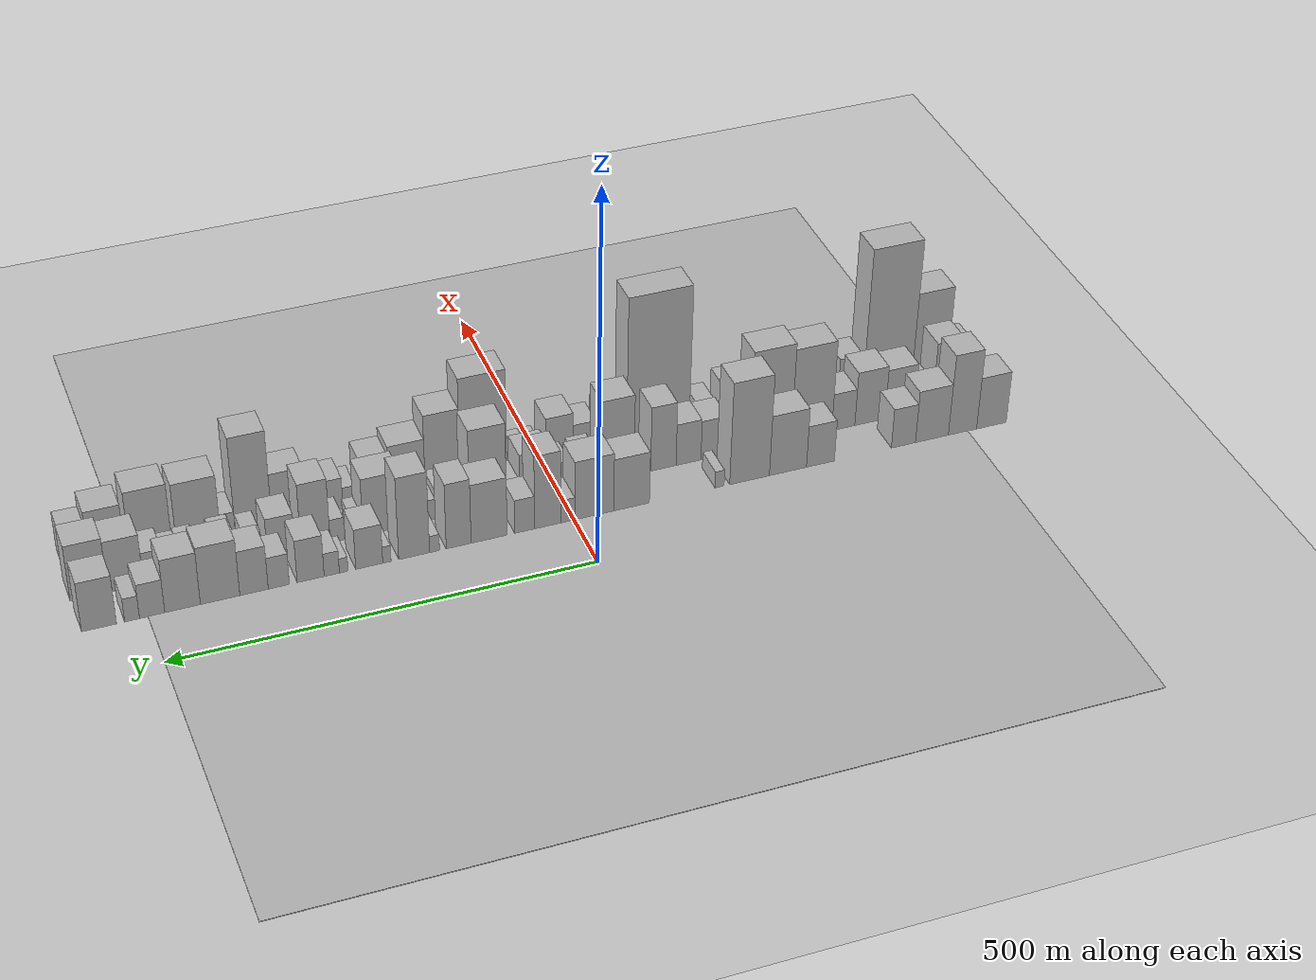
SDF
<?xml version="1.0" encoding="utf-8"?>

<sdf version="1.6">

   <world name="default">

      <gui fullscreen="0">

         <camera name="user_camera">

            <pose>-15 0 4.57585 0 0 0</pose>

            <view_controller>orbit</view_controller>

         </camera>

      </gui>

      <scene>

         <sky>

           <clouds>

             <speed>12</speed>

           </clouds>

         </sky>

         <ambient>0.4 0.4 0.4 1</ambient>

         <background>0.7 0.7 0.7 1</background>

         <shadows>1</shadows>

      </scene>

      <gravity>0 0 -9.8066</gravity>

      <magnetic_field>6e-06 2.3e-05 -4.2e-05</magnetic_field>

      <physics default="0" name="default_physics" type="ode">

         <ode>

            <solver>

               <type>quick</type>

               <iters>10</iters>

               <sor>1.0</sor>

               <use_dynamic_moi_rescaling>0</use_dynamic_moi_rescaling>

            </solver>

            <constraints>

               <cfm>0</cfm>

               <erp>0.2</erp>

               <contact_max_correcting_vel>100</contact_max_correcting_vel>

               <contact_surface_layer>0.001</contact_surface_layer>

            </constraints>

         </ode>

         <max_step_size>0.004</max_step_size>

         <real_time_factor>1</real_time_factor>

         <real_time_update_rate>250</real_time_update_rate>

      </physics>

      <light name="sun" type="directional">

         <cast_shadows>1</cast_shadows>

         <pose>0 0 10 0 0 0</pose>

         <diffuse>0.8 0.8 0.8 1</diffuse>

         <specular>0.2 0.2 0.2 1</specular>

         <attenuation>

            <range>1000</range>

            <constant>0.9</constant>

            <linear>0.01</linear>

            <quadratic>0.001</quadratic>

         </attenuation>

         <direction>-0.5 0.1 -0.9</direction>

      </light>

      <include>

         <name>ground_plane_1</name>

         <uri>model://HANNAS_ground_plane</uri>

         <pose>0 0 0  0 0 0</pose>

      </include>

      <include>

         <name>ground_plane_2</name>

         <uri>model://HANNAS_ground_plane</uri>

         <pose>100 0 0  0 0 0</pose>

      </include>

      <model name="building_1">

         <static>1</static>

         <pose frame="">100.0000 -531.3328 0 0.000000 0.000000 0.000000</pose>

         <link name="link">

            <pose frame="">0 0 37.50 0 0 0</pose>

            <collision name="collision">

               <geometry>

                  <box>

                     <size>40.0000 39.3343 75.0000</size>

                  </box>

               </geometry>

               <max_contacts>10</max_contacts>

               <surface>

                  <contact>

                     <ode/>

                  </contact>

                  <bounce/>

                  <friction>

                     <torsional>

                        <ode/>

                     </torsional>

                     <ode/>

                  </friction>

               </surface>

            </collision>

            <visual name="visual">

               <cast_shadows>0</cast_shadows>

               <geometry>

                  <box>

                     <size>40.0000 39.3343 75.0000</size>

                  </box>

               </geometry>

               <material>

                  <script>

                     <uri>model://HANNAS_wall/materials/scripts</uri>

                     <uri>model://HANNAS_wall/materials/textures</uri>

                     <name>vrc/HANNAS_wall</name>

                  </script>

               </material>

            </visual>

            <self_collide>0</self_collide>

            <enable_wind>0</enable_wind>

            <kinematic>0</kinematic>

         </link>

      </model>

      <model name="building_2">

         <static>1</static>

         <pose frame="">100.0000 -492.9887 0 0.000000 0.000000 0.000000</pose>

         <link name="link">

            <pose frame="">0 0 58.50 0 0 0</pose>

            <collision name="collision">

               <geometry>

                  <box>

                     <size>40.0000 37.3539 117.0000</size>

                  </box>

               </geometry>

               <max_contacts>10</max_contacts>

               <surface>

                  <contact>

                     <ode/>

                  </contact>

                  <bounce/>

                  <friction>

                     <torsional>

                        <ode/>

                     </torsional>

                     <ode/>

                  </friction>

               </surface>

            </collision>

            <visual name="visual">

               <cast_shadows>0</cast_shadows>

               <geometry>

                  <box>

                     <size>40.0000 37.3539 117.0000</size>

                  </box>

               </geometry>

               <material>

                  <script>

                     <uri>model://HANNAS_wall/materials/scripts</uri>

                     <uri>model://HANNAS_wall/materials/textures</uri>

                     <name>vrc/HANNAS_wall</name>

                  </script>

               </material>

            </visual>

            <self_collide>0</self_collide>

            <enable_wind>0</enable_wind>

            <kinematic>0</kinematic>

         </link>

      </model>

      <model name="building_3">

         <static>1</static>

         <pose frame="">100.0000 -452.7107 0 0.000000 0.000000 0.000000</pose>

         <link name="link">

            <pose frame="">0 0 37.50 0 0 0</pose>

            <collision name="collision">

               <geometry>

                  <box>

                     <size>40.0000 43.2021 75.0000</size>

                  </box>

               </geometry>

               <max_contacts>10</max_contacts>

               <surface>

                  <contact>

                     <ode/>

                  </contact>

                  <bounce/>

                  <friction>

                     <torsional>

                        <ode/>

                     </torsional>

                     <ode/>

                  </friction>

               </surface>

            </collision>

            <visual name="visual">

               <cast_shadows>0</cast_shadows>

               <geometry>

                  <box>

                     <size>40.0000 43.2021 75.0000</size>

                  </box>

               </geometry>

               <material>

                  <script>

                     <uri>model://HANNAS_wall/materials/scripts</uri>

                     <uri>model://HANNAS_wall/materials/textures</uri>

                     <name>vrc/HANNAS_wall</name>

                  </script>

               </material>

            </visual>

            <self_collide>0</self_collide>

            <enable_wind>0</enable_wind>

            <kinematic>0</kinematic>

         </link>

      </model>

      <model name="building_4">

         <static>1</static>

         <pose frame="">100.0000 -415.3663 0 0.000000 0.000000 0.000000</pose>

         <link name="link">

            <pose frame="">0 0 28.50 0 0 0</pose>

            <collision name="collision">

               <geometry>

                  <box>

                     <size>40.0000 31.4868 57.0000</size>

                  </box>

               </geometry>

               <max_contacts>10</max_contacts>

               <surface>

                  <contact>

                     <ode/>

                  </contact>

                  <bounce/>

                  <friction>

                     <torsional>

                        <ode/>

                     </torsional>

                     <ode/>

                  </friction>

               </surface>

            </collision>

            <visual name="visual">

               <cast_shadows>0</cast_shadows>

               <geometry>

                  <box>

                     <size>40.0000 31.4868 57.0000</size>

                  </box>

               </geometry>

               <material>

                  <script>

                     <uri>model://HANNAS_wall/materials/scripts</uri>

                     <uri>model://HANNAS_wall/materials/textures</uri>

                     <name>vrc/HANNAS_wall</name>

                  </script>

               </material>

            </visual>

            <self_collide>0</self_collide>

            <enable_wind>0</enable_wind>

            <kinematic>0</kinematic>

         </link>

      </model>

      <model name="building_5">

         <static>1</static>

         <pose frame="">100.0000 -307.8928 0 0.000000 0.000000 0.000000</pose>

         <link name="link">

            <pose frame="">0 0 30.00 0 0 0</pose>

            <collision name="collision">

               <geometry>

                  <box>

                     <size>40.0000 35.8201 60.0000</size>

                  </box>

               </geometry>

               <max_contacts>10</max_contacts>

               <surface>

                  <contact>

                     <ode/>

                  </contact>

                  <bounce/>

                  <friction>

                     <torsional>

                        <ode/>

                     </torsional>

                     <ode/>

                  </friction>

               </surface>

            </collision>

            <visual name="visual">

               <cast_shadows>0</cast_shadows>

               <geometry>

                  <box>

                     <size>40.0000 35.8201 60.0000</size>

                  </box>

               </geometry>

               <material>

                  <script>

                     <uri>model://HANNAS_wall/materials/scripts</uri>

                     <uri>model://HANNAS_wall/materials/textures</uri>

                     <name>vrc/HANNAS_wall</name>

                  </script>

               </material>

            </visual>

            <self_collide>0</self_collide>

            <enable_wind>0</enable_wind>

            <kinematic>0</kinematic>

         </link>

      </model>

      <model name="building_6">

         <static>1</static>

         <pose frame="">100.0000 -266.3477 0 0.000000 0.000000 0.000000</pose>

         <link name="link">

            <pose frame="">0 0 43.50 0 0 0</pose>

            <collision name="collision">

               <geometry>

                  <box>

                     <size>40.0000 47.2701 87.0000</size>

                  </box>

               </geometry>

               <max_contacts>10</max_contacts>

               <surface>

                  <contact>

                     <ode/>

                  </contact>

                  <bounce/>

                  <friction>

                     <torsional>

                        <ode/>

                     </torsional>

                     <ode/>

                  </friction>

               </surface>

            </collision>

            <visual name="visual">

               <cast_shadows>0</cast_shadows>

               <geometry>

                  <box>

                     <size>40.0000 47.2701 87.0000</size>

                  </box>

               </geometry>

               <material>

                  <script>

                     <uri>model://HANNAS_wall/materials/scripts</uri>

                     <uri>model://HANNAS_wall/materials/textures</uri>

                     <name>vrc/HANNAS_wall</name>

                  </script>

               </material>

            </visual>

            <self_collide>0</self_collide>

            <enable_wind>0</enable_wind>

            <kinematic>0</kinematic>

         </link>

      </model>

      <model name="building_7">

         <static>1</static>

         <pose frame="">100.0000 -217.5453 0 0.000000 0.000000 0.000000</pose>

         <link name="link">

            <pose frame="">0 0 73.50 0 0 0</pose>

            <collision name="collision">

               <geometry>

                  <box>

                     <size>40.0000 50.3349 147.0000</size>

                  </box>

               </geometry>

               <max_contacts>10</max_contacts>

               <surface>

                  <contact>

                     <ode/>

                  </contact>

                  <bounce/>

                  <friction>

                     <torsional>

                        <ode/>

                     </torsional>

                     <ode/>

                  </friction>

               </surface>

            </collision>

            <visual name="visual">

               <cast_shadows>0</cast_shadows>

               <geometry>

                  <box>

                     <size>40.0000 50.3349 147.0000</size>

                  </box>

               </geometry>

               <material>

                  <script>

                     <uri>model://HANNAS_wall/materials/scripts</uri>

                     <uri>model://HANNAS_wall/materials/textures</uri>

                     <name>vrc/HANNAS_wall</name>

                  </script>

               </material>

            </visual>

            <self_collide>0</self_collide>

            <enable_wind>0</enable_wind>

            <kinematic>0</kinematic>

         </link>

      </model>

      <model name="building_8">

         <static>1</static>

         <pose frame="">100.0000 -179.6727 0 0.000000 0.000000 0.000000</pose>

         <link name="link">

            <pose frame="">0 0 12.00 0 0 0</pose>

            <collision name="collision">

               <geometry>

                  <box>

                     <size>40.0000 11.4102 24.0000</size>

                  </box>

               </geometry>

               <max_contacts>10</max_contacts>

               <surface>

                  <contact>

                     <ode/>

                  </contact>

                  <bounce/>

                  <friction>

                     <torsional>

                        <ode/>

                     </torsional>

                     <ode/>

                  </friction>

               </surface>

            </collision>

            <visual name="visual">

               <cast_shadows>0</cast_shadows>

               <geometry>

                  <box>

                     <size>40.0000 11.4102 24.0000</size>

                  </box>

               </geometry>

               <material>

                  <script>

                     <uri>model://HANNAS_wall/materials/scripts</uri>

                     <uri>model://HANNAS_wall/materials/textures</uri>

                     <name>vrc/HANNAS_wall</name>

                  </script>

               </material>

            </visual>

            <self_collide>0</self_collide>

            <enable_wind>0</enable_wind>

            <kinematic>0</kinematic>

         </link>

      </model>

      <model name="building_9">

         <static>1</static>

         <pose frame="">100.0000 -69.9859 0 0.000000 0.000000 0.000000</pose>

         <link name="link">

            <pose frame="">0 0 37.50 0 0 0</pose>

            <collision name="collision">

               <geometry>

                  <box>

                     <size>40.0000 43.9879 75.0000</size>

                  </box>

               </geometry>

               <max_contacts>10</max_contacts>

               <surface>

                  <contact>

                     <ode/>

                  </contact>

                  <bounce/>

                  <friction>

                     <torsional>

                        <ode/>

                     </torsional>

                     <ode/>

                  </friction>

               </surface>

            </collision>

            <visual name="visual">

               <cast_shadows>0</cast_shadows>

               <geometry>

                  <box>

                     <size>40.0000 43.9879 75.0000</size>

                  </box>

               </geometry>

               <material>

                  <script>

                     <uri>model://HANNAS_wall/materials/scripts</uri>

                     <uri>model://HANNAS_wall/materials/textures</uri>

                     <name>vrc/HANNAS_wall</name>

                  </script>

               </material>

            </visual>

            <self_collide>0</self_collide>

            <enable_wind>0</enable_wind>

            <kinematic>0</kinematic>

         </link>

      </model>

      <model name="building_10">

         <static>1</static>

         <pose frame="">100.0000 -24.0479 0 0.000000 0.000000 0.000000</pose>

         <link name="link">

            <pose frame="">0 0 42.00 0 0 0</pose>

            <collision name="collision">

               <geometry>

                  <box>

                     <size>40.0000 47.8881 84.0000</size>

                  </box>

               </geometry>

               <max_contacts>10</max_contacts>

               <surface>

                  <contact>

                     <ode/>

                  </contact>

                  <bounce/>

                  <friction>

                     <torsional>

                        <ode/>

                     </torsional>

                     <ode/>

                  </friction>

               </surface>

            </collision>

            <visual name="visual">

               <cast_shadows>0</cast_shadows>

               <geometry>

                  <box>

                     <size>40.0000 47.8881 84.0000</size>

                  </box>

               </geometry>

               <material>

                  <script>

                     <uri>model://HANNAS_wall/materials/scripts</uri>

                     <uri>model://HANNAS_wall/materials/textures</uri>

                     <name>vrc/HANNAS_wall</name>

                  </script>

               </material>

            </visual>

            <self_collide>0</self_collide>

            <enable_wind>0</enable_wind>

            <kinematic>0</kinematic>

         </link>

      </model>

      <model name="building_11">

         <static>1</static>

         <pose frame="">100.0000 8.4492 0 0.000000 0.000000 0.000000</pose>

         <link name="link">

            <pose frame="">0 0 16.50 0 0 0</pose>

            <collision name="collision">

               <geometry>

                  <box>

                     <size>40.0000 17.1060 33.0000</size>

                  </box>

               </geometry>

               <max_contacts>10</max_contacts>

               <surface>

                  <contact>

                     <ode/>

                  </contact>

                  <bounce/>

                  <friction>

                     <torsional>

                        <ode/>

                     </torsional>

                     <ode/>

                  </friction>

               </surface>

            </collision>

            <visual name="visual">

               <cast_shadows>0</cast_shadows>

               <geometry>

                  <box>

                     <size>40.0000 17.1060 33.0000</size>

                  </box>

               </geometry>

               <material>

                  <script>

                     <uri>model://HANNAS_wall/materials/scripts</uri>

                     <uri>model://HANNAS_wall/materials/textures</uri>

                     <name>vrc/HANNAS_wall</name>

                  </script>

               </material>

            </visual>

            <self_collide>0</self_collide>

            <enable_wind>0</enable_wind>

            <kinematic>0</kinematic>

         </link>

      </model>

      <model name="building_12">

         <static>1</static>

         <pose frame="">100.0000 32.9279 0 0.000000 0.000000 0.000000</pose>

         <link name="link">

            <pose frame="">0 0 52.50 0 0 0</pose>

            <collision name="collision">

               <geometry>

                  <box>

                     <size>40.0000 31.8514 105.0000</size>

                  </box>

               </geometry>

               <max_contacts>10</max_contacts>

               <surface>

                  <contact>

                     <ode/>

                  </contact>

                  <bounce/>

                  <friction>

                     <torsional>

                        <ode/>

                     </torsional>

                     <ode/>

                  </friction>

               </surface>

            </collision>

            <visual name="visual">

               <cast_shadows>0</cast_shadows>

               <geometry>

                  <box>

                     <size>40.0000 31.8514 105.0000</size>

                  </box>

               </geometry>

               <material>

                  <script>

                     <uri>model://HANNAS_wall/materials/scripts</uri>

                     <uri>model://HANNAS_wall/materials/textures</uri>

                     <name>vrc/HANNAS_wall</name>

                  </script>

               </material>

            </visual>

            <self_collide>0</self_collide>

            <enable_wind>0</enable_wind>

            <kinematic>0</kinematic>

         </link>

      </model>

      <model name="building_13">

         <static>1</static>

         <pose frame="">100.0000 60.9110 0 0.000000 0.000000 0.000000</pose>

         <link name="link">

            <pose frame="">0 0 24.00 0 0 0</pose>

            <collision name="collision">

               <geometry>

                  <box>

                     <size>40.0000 24.1148 48.0000</size>

                  </box>

               </geometry>

               <max_contacts>10</max_contacts>

               <surface>

                  <contact>

                     <ode/>

                  </contact>

                  <bounce/>

                  <friction>

                     <torsional>

                        <ode/>

                     </torsional>

                     <ode/>

                  </friction>

               </surface>

            </collision>

            <visual name="visual">

               <cast_shadows>0</cast_shadows>

               <geometry>

                  <box>

                     <size>40.0000 24.1148 48.0000</size>

                  </box>

               </geometry>

               <material>

                  <script>

                     <uri>model://HANNAS_wall/materials/scripts</uri>

                     <uri>model://HANNAS_wall/materials/textures</uri>

                     <name>vrc/HANNAS_wall</name>

                  </script>

               </material>

            </visual>

            <self_collide>0</self_collide>

            <enable_wind>0</enable_wind>

            <kinematic>0</kinematic>

         </link>

      </model>

      <model name="building_14">

         <static>1</static>

         <pose frame="">100.0000 103.5865 0 0.000000 0.000000 0.000000</pose>

         <link name="link">

            <pose frame="">0 0 42.00 0 0 0</pose>

            <collision name="collision">

               <geometry>

                  <box>

                     <size>40.0000 43.2362 84.0000</size>

                  </box>

               </geometry>

               <max_contacts>10</max_contacts>

               <surface>

                  <contact>

                     <ode/>

                  </contact>

                  <bounce/>

                  <friction>

                     <torsional>

                        <ode/>

                     </torsional>

                     <ode/>

                  </friction>

               </surface>

            </collision>

            <visual name="visual">

               <cast_shadows>0</cast_shadows>

               <geometry>

                  <box>

                     <size>40.0000 43.2362 84.0000</size>

                  </box>

               </geometry>

               <material>

                  <script>

                     <uri>model://HANNAS_wall/materials/scripts</uri>

                     <uri>model://HANNAS_wall/materials/textures</uri>

                     <name>vrc/HANNAS_wall</name>

                  </script>

               </material>

            </visual>

            <self_collide>0</self_collide>

            <enable_wind>0</enable_wind>

            <kinematic>0</kinematic>

         </link>

      </model>

      <model name="building_15">

         <static>1</static>

         <pose frame="">100.0000 140.0767 0 0.000000 0.000000 0.000000</pose>

         <link name="link">

            <pose frame="">0 0 46.50 0 0 0</pose>

            <collision name="collision">

               <geometry>

                  <box>

                     <size>40.0000 29.7441 93.0000</size>

                  </box>

               </geometry>

               <max_contacts>10</max_contacts>

               <surface>

                  <contact>

                     <ode/>

                  </contact>

                  <bounce/>

                  <friction>

                     <torsional>

                        <ode/>

                     </torsional>

                     <ode/>

                  </friction>

               </surface>

            </collision>

            <visual name="visual">

               <cast_shadows>0</cast_shadows>

               <geometry>

                  <box>

                     <size>40.0000 29.7441 93.0000</size>

                  </box>

               </geometry>

               <material>

                  <script>

                     <uri>model://HANNAS_wall/materials/scripts</uri>

                     <uri>model://HANNAS_wall/materials/textures</uri>

                     <name>vrc/HANNAS_wall</name>

                  </script>

               </material>

            </visual>

            <self_collide>0</self_collide>

            <enable_wind>0</enable_wind>

            <kinematic>0</kinematic>

         </link>

      </model>

      <model name="building_16">

         <static>1</static>

         <pose frame="">100.0000 168.8575 0 0.000000 0.000000 0.000000</pose>

         <link name="link">

            <pose frame="">0 0 12.00 0 0 0</pose>

            <collision name="collision">

               <geometry>

                  <box>

                     <size>40.0000 11.8175 24.0000</size>

                  </box>

               </geometry>

               <max_contacts>10</max_contacts>

               <surface>

                  <contact>

                     <ode/>

                  </contact>

                  <bounce/>

                  <friction>

                     <torsional>

                        <ode/>

                     </torsional>

                     <ode/>

                  </friction>

               </surface>

            </collision>

            <visual name="visual">

               <cast_shadows>0</cast_shadows>

               <geometry>

                  <box>

                     <size>40.0000 11.8175 24.0000</size>

                  </box>

               </geometry>

               <material>

                  <script>

                     <uri>model://HANNAS_wall/materials/scripts</uri>

                     <uri>model://HANNAS_wall/materials/textures</uri>

                     <name>vrc/HANNAS_wall</name>

                  </script>

               </material>

            </visual>

            <self_collide>0</self_collide>

            <enable_wind>0</enable_wind>

            <kinematic>0</kinematic>

         </link>

      </model>

      <model name="building_17">

         <static>1</static>

         <pose frame="">100.0000 193.0246 0 0.000000 0.000000 0.000000</pose>

         <link name="link">

            <pose frame="">0 0 58.50 0 0 0</pose>

            <collision name="collision">

               <geometry>

                  <box>

                     <size>40.0000 36.5165 117.0000</size>

                  </box>

               </geometry>

               <max_contacts>10</max_contacts>

               <surface>

                  <contact>

                     <ode/>

                  </contact>

                  <bounce/>

                  <friction>

                     <torsional>

                        <ode/>

                     </torsional>

                     <ode/>

                  </friction>

               </surface>

            </collision>

            <visual name="visual">

               <cast_shadows>0</cast_shadows>

               <geometry>

                  <box>

                     <size>40.0000 36.5165 117.0000</size>

                  </box>

               </geometry>

               <material>

                  <script>

                     <uri>model://HANNAS_wall/materials/scripts</uri>

                     <uri>model://HANNAS_wall/materials/textures</uri>

                     <name>vrc/HANNAS_wall</name>

                  </script>

               </material>

            </visual>

            <self_collide>0</self_collide>

            <enable_wind>0</enable_wind>

            <kinematic>0</kinematic>

         </link>

      </model>

      <model name="building_18">

         <static>1</static>

         <pose frame="">100.0000 225.1715 0 0.000000 0.000000 0.000000</pose>

         <link name="link">

            <pose frame="">0 0 12.00 0 0 0</pose>

            <collision name="collision">

               <geometry>

                  <box>

                     <size>40.0000 9.7774 24.0000</size>

                  </box>

               </geometry>

               <max_contacts>10</max_contacts>

               <surface>

                  <contact>

                     <ode/>

                  </contact>

                  <bounce/>

                  <friction>

                     <torsional>

                        <ode/>

                     </torsional>

                     <ode/>

                  </friction>

               </surface>

            </collision>

            <visual name="visual">

               <cast_shadows>0</cast_shadows>

               <geometry>

                  <box>

                     <size>40.0000 9.7774 24.0000</size>

                  </box>

               </geometry>

               <material>

                  <script>

                     <uri>model://HANNAS_wall/materials/scripts</uri>

                     <uri>model://HANNAS_wall/materials/textures</uri>

                     <name>vrc/HANNAS_wall</name>

                  </script>

               </material>

            </visual>

            <self_collide>0</self_collide>

            <enable_wind>0</enable_wind>

            <kinematic>0</kinematic>

         </link>

      </model>

      <model name="building_19">

         <static>1</static>

         <pose frame="">100.0000 245.9627 0 0.000000 0.000000 0.000000</pose>

         <link name="link">

            <pose frame="">0 0 28.50 0 0 0</pose>

            <collision name="collision">

               <geometry>

                  <box>

                     <size>40.0000 31.8050 57.0000</size>

                  </box>

               </geometry>

               <max_contacts>10</max_contacts>

               <surface>

                  <contact>

                     <ode/>

                  </contact>

                  <bounce/>

                  <friction>

                     <torsional>

                        <ode/>

                     </torsional>

                     <ode/>

                  </friction>

               </surface>

            </collision>

            <visual name="visual">

               <cast_shadows>0</cast_shadows>

               <geometry>

                  <box>

                     <size>40.0000 31.8050 57.0000</size>

                  </box>

               </geometry>

               <material>

                  <script>

                     <uri>model://HANNAS_wall/materials/scripts</uri>

                     <uri>model://HANNAS_wall/materials/textures</uri>

                     <name>vrc/HANNAS_wall</name>

                  </script>

               </material>

            </visual>

            <self_collide>0</self_collide>

            <enable_wind>0</enable_wind>

            <kinematic>0</kinematic>

         </link>

      </model>

      <model name="building_20">

         <static>1</static>

         <pose frame="">100.0000 275.8866 0 0.000000 0.000000 0.000000</pose>

         <link name="link">

            <pose frame="">0 0 10.50 0 0 0</pose>

            <collision name="collision">

               <geometry>

                  <box>

                     <size>40.0000 10.0427 21.0000</size>

                  </box>

               </geometry>

               <max_contacts>10</max_contacts>

               <surface>

                  <contact>

                     <ode/>

                  </contact>

                  <bounce/>

                  <friction>

                     <torsional>

                        <ode/>

                     </torsional>

                     <ode/>

                  </friction>

               </surface>

            </collision>

            <visual name="visual">

               <cast_shadows>0</cast_shadows>

               <geometry>

                  <box>

                     <size>40.0000 10.0427 21.0000</size>

                  </box>

               </geometry>

               <material>

                  <script>

                     <uri>model://HANNAS_wall/materials/scripts</uri>

                     <uri>model://HANNAS_wall/materials/textures</uri>

                     <name>vrc/HANNAS_wall</name>

                  </script>

               </material>

            </visual>

            <self_collide>0</self_collide>

            <enable_wind>0</enable_wind>

            <kinematic>0</kinematic>

         </link>

      </model>

      <model name="building_21">

         <static>1</static>

         <pose frame="">100.0000 289.7496 0 0.000000 0.000000 0.000000</pose>

         <link name="link">

            <pose frame="">0 0 16.50 0 0 0</pose>

            <collision name="collision">

               <geometry>

                  <box>

                     <size>40.0000 17.6834 33.0000</size>

                  </box>

               </geometry>

               <max_contacts>10</max_contacts>

               <surface>

                  <contact>

                     <ode/>

                  </contact>

                  <bounce/>

                  <friction>

                     <torsional>

                        <ode/>

                     </torsional>

                     <ode/>

                  </friction>

               </surface>

            </collision>

            <visual name="visual">

               <cast_shadows>0</cast_shadows>

               <geometry>

                  <box>

                     <size>40.0000 17.6834 33.0000</size>

                  </box>

               </geometry>

               <material>

                  <script>

                     <uri>model://HANNAS_wall/materials/scripts</uri>

                     <uri>model://HANNAS_wall/materials/textures</uri>

                     <name>vrc/HANNAS_wall</name>

                  </script>

               </material>

            </visual>

            <self_collide>0</self_collide>

            <enable_wind>0</enable_wind>

            <kinematic>0</kinematic>

         </link>

      </model>

      <model name="building_22">

         <static>1</static>

         <pose frame="">100.0000 314.2747 0 0.000000 0.000000 0.000000</pose>

         <link name="link">

            <pose frame="">0 0 30.00 0 0 0</pose>

            <collision name="collision">

               <geometry>

                  <box>

                     <size>40.0000 31.3669 60.0000</size>

                  </box>

               </geometry>

               <max_contacts>10</max_contacts>

               <surface>

                  <contact>

                     <ode/>

                  </contact>

                  <bounce/>

                  <friction>

                     <torsional>

                        <ode/>

                     </torsional>

                     <ode/>

                  </friction>

               </surface>

            </collision>

            <visual name="visual">

               <cast_shadows>0</cast_shadows>

               <geometry>

                  <box>

                     <size>40.0000 31.3669 60.0000</size>

                  </box>

               </geometry>

               <material>

                  <script>

                     <uri>model://HANNAS_wall/materials/scripts</uri>

                     <uri>model://HANNAS_wall/materials/textures</uri>

                     <name>vrc/HANNAS_wall</name>

                  </script>

               </material>

            </visual>

            <self_collide>0</self_collide>

            <enable_wind>0</enable_wind>

            <kinematic>0</kinematic>

         </link>

      </model>

      <model name="building_23">

         <static>1</static>

         <pose frame="">100.0000 351.1268 0 0.000000 0.000000 0.000000</pose>

         <link name="link">

            <pose frame="">0 0 22.50 0 0 0</pose>

            <collision name="collision">

               <geometry>

                  <box>

                     <size>40.0000 24.3372 45.0000</size>

                  </box>

               </geometry>

               <max_contacts>10</max_contacts>

               <surface>

                  <contact>

                     <ode/>

                  </contact>

                  <bounce/>

                  <friction>

                     <torsional>

                        <ode/>

                     </torsional>

                     <ode/>

                  </friction>

               </surface>

            </collision>

            <visual name="visual">

               <cast_shadows>0</cast_shadows>

               <geometry>

                  <box>

                     <size>40.0000 24.3372 45.0000</size>

                  </box>

               </geometry>

               <material>

                  <script>

                     <uri>model://HANNAS_wall/materials/scripts</uri>

                     <uri>model://HANNAS_wall/materials/textures</uri>

                     <name>vrc/HANNAS_wall</name>

                  </script>

               </material>

            </visual>

            <self_collide>0</self_collide>

            <enable_wind>0</enable_wind>

            <kinematic>0</kinematic>

         </link>

      </model>

      <model name="building_24">

         <static>1</static>

         <pose frame="">100.0000 379.5723 0 0.000000 0.000000 0.000000</pose>

         <link name="link">

            <pose frame="">0 0 31.50 0 0 0</pose>

            <collision name="collision">

               <geometry>

                  <box>

                     <size>40.0000 32.5538 63.0000</size>

                  </box>

               </geometry>

               <max_contacts>10</max_contacts>

               <surface>

                  <contact>

                     <ode/>

                  </contact>

                  <bounce/>

                  <friction>

                     <torsional>

                        <ode/>

                     </torsional>

                     <ode/>

                  </friction>

               </surface>

            </collision>

            <visual name="visual">

               <cast_shadows>0</cast_shadows>

               <geometry>

                  <box>

                     <size>40.0000 32.5538 63.0000</size>

                  </box>

               </geometry>

               <material>

                  <script>

                     <uri>model://HANNAS_wall/materials/scripts</uri>

                     <uri>model://HANNAS_wall/materials/textures</uri>

                     <name>vrc/HANNAS_wall</name>

                  </script>

               </material>

            </visual>

            <self_collide>0</self_collide>

            <enable_wind>0</enable_wind>

            <kinematic>0</kinematic>

         </link>

      </model>

      <model name="building_25">

         <static>1</static>

         <pose frame="">100.0000 418.3268 0 0.000000 0.000000 0.000000</pose>

         <link name="link">

            <pose frame="">0 0 40.50 0 0 0</pose>

            <collision name="collision">

               <geometry>

                  <box>

                     <size>40.0000 44.9550 81.0000</size>

                  </box>

               </geometry>

               <max_contacts>10</max_contacts>

               <surface>

                  <contact>

                     <ode/>

                  </contact>

                  <bounce/>

                  <friction>

                     <torsional>

                        <ode/>

                     </torsional>

                     <ode/>

                  </friction>

               </surface>

            </collision>

            <visual name="visual">

               <cast_shadows>0</cast_shadows>

               <geometry>

                  <box>

                     <size>40.0000 44.9550 81.0000</size>

                  </box>

               </geometry>

               <material>

                  <script>

                     <uri>model://HANNAS_wall/materials/scripts</uri>

                     <uri>model://HANNAS_wall/materials/textures</uri>

                     <name>vrc/HANNAS_wall</name>

                  </script>

               </material>

            </visual>

            <self_collide>0</self_collide>

            <enable_wind>0</enable_wind>

            <kinematic>0</kinematic>

         </link>

      </model>

      <model name="building_26">

         <static>1</static>

         <pose frame="">100.0000 460.9864 0 0.000000 0.000000 0.000000</pose>

         <link name="link">

            <pose frame="">0 0 37.50 0 0 0</pose>

            <collision name="collision">

               <geometry>

                  <box>

                     <size>40.0000 40.3642 75.0000</size>

                  </box>

               </geometry>

               <max_contacts>10</max_contacts>

               <surface>

                  <contact>

                     <ode/>

                  </contact>

                  <bounce/>

                  <friction>

                     <torsional>

                        <ode/>

                     </torsional>

                     <ode/>

                  </friction>

               </surface>

            </collision>

            <visual name="visual">

               <cast_shadows>0</cast_shadows>

               <geometry>

                  <box>

                     <size>40.0000 40.3642 75.0000</size>

                  </box>

               </geometry>

               <material>

                  <script>

                     <uri>model://HANNAS_wall/materials/scripts</uri>

                     <uri>model://HANNAS_wall/materials/textures</uri>

                     <name>vrc/HANNAS_wall</name>

                  </script>

               </material>

            </visual>

            <self_collide>0</self_collide>

            <enable_wind>0</enable_wind>

            <kinematic>0</kinematic>

         </link>

      </model>

      <model name="building_27">

         <static>1</static>

         <pose frame="">100.0000 495.3992 0 0.000000 0.000000 0.000000</pose>

         <link name="link">

            <pose frame="">0 0 24.00 0 0 0</pose>

            <collision name="collision">

               <geometry>

                  <box>

                     <size>40.0000 28.4614 48.0000</size>

                  </box>

               </geometry>

               <max_contacts>10</max_contacts>

               <surface>

                  <contact>

                     <ode/>

                  </contact>

                  <bounce/>

                  <friction>

                     <torsional>

                        <ode/>

                     </torsional>

                     <ode/>

                  </friction>

               </surface>

            </collision>

            <visual name="visual">

               <cast_shadows>0</cast_shadows>

               <geometry>

                  <box>

                     <size>40.0000 28.4614 48.0000</size>

                  </box>

               </geometry>

               <material>

                  <script>

                     <uri>model://HANNAS_wall/materials/scripts</uri>

                     <uri>model://HANNAS_wall/materials/textures</uri>

                     <name>vrc/HANNAS_wall</name>

                  </script>

               </material>

            </visual>

            <self_collide>0</self_collide>

            <enable_wind>0</enable_wind>

            <kinematic>0</kinematic>

         </link>

      </model>

      <model name="building_28">

         <static>1</static>

         <pose frame="">100.0000 517.9924 0 0.000000 0.000000 0.000000</pose>

         <link name="link">

            <pose frame="">0 0 16.50 0 0 0</pose>

            <collision name="collision">

               <geometry>

                  <box>

                     <size>40.0000 16.7249 33.0000</size>

                  </box>

               </geometry>

               <max_contacts>10</max_contacts>

               <surface>

                  <contact>

                     <ode/>

                  </contact>

                  <bounce/>

                  <friction>

                     <torsional>

                        <ode/>

                     </torsional>

                     <ode/>

                  </friction>

               </surface>

            </collision>

            <visual name="visual">

               <cast_shadows>0</cast_shadows>

               <geometry>

                  <box>

                     <size>40.0000 16.7249 33.0000</size>

                  </box>

               </geometry>

               <material>

                  <script>

                     <uri>model://HANNAS_wall/materials/scripts</uri>

                     <uri>model://HANNAS_wall/materials/textures</uri>

                     <name>vrc/HANNAS_wall</name>

                  </script>

               </material>

            </visual>

            <self_collide>0</self_collide>

            <enable_wind>0</enable_wind>

            <kinematic>0</kinematic>

         </link>

      </model>

      <model name="building_29">

         <static>1</static>

         <pose frame="">100.0000 554.8969 0 0.000000 0.000000 0.000000</pose>

         <link name="link">

            <pose frame="">0 0 34.50 0 0 0</pose>

            <collision name="collision">

               <geometry>

                  <box>

                     <size>40.0000 39.0842 69.0000</size>

                  </box>

               </geometry>

               <max_contacts>10</max_contacts>

               <surface>

                  <contact>

                     <ode/>

                  </contact>

                  <bounce/>

                  <friction>

                     <torsional>

                        <ode/>

                     </torsional>

                     <ode/>

                  </friction>

               </surface>

            </collision>

            <visual name="visual">

               <cast_shadows>0</cast_shadows>

               <geometry>

                  <box>

                     <size>40.0000 39.0842 69.0000</size>

                  </box>

               </geometry>

               <material>

                  <script>

                     <uri>model://HANNAS_wall/materials/scripts</uri>

                     <uri>model://HANNAS_wall/materials/textures</uri>

                     <name>vrc/HANNAS_wall</name>

                  </script>

               </material>

            </visual>

            <self_collide>0</self_collide>

            <enable_wind>0</enable_wind>

            <kinematic>0</kinematic>

         </link>

      </model>

      <model name="building_30">

         <static>1</static>

         <pose frame="">155.0000 -540.3779 0 0.000000 0.000000 0.000000</pose>

         <link name="link">

            <pose frame="">0 0 24.00 0 0 0</pose>

            <collision name="collision">

               <geometry>

                  <box>

                     <size>40.0000 25.2442 48.0000</size>

                  </box>

               </geometry>

               <max_contacts>10</max_contacts>

               <surface>

                  <contact>

                     <ode/>

                  </contact>

                  <bounce/>

                  <friction>

                     <torsional>

                        <ode/>

                     </torsional>

                     <ode/>

                  </friction>

               </surface>

            </collision>

            <visual name="visual">

               <cast_shadows>0</cast_shadows>

               <geometry>

                  <box>

                     <size>40.0000 25.2442 48.0000</size>

                  </box>

               </geometry>

               <material>

                  <script>

                     <uri>model://HANNAS_wall/materials/scripts</uri>

                     <uri>model://HANNAS_wall/materials/textures</uri>

                     <name>vrc/HANNAS_wall</name>

                  </script>

               </material>

            </visual>

            <self_collide>0</self_collide>

            <enable_wind>0</enable_wind>

            <kinematic>0</kinematic>

         </link>

      </model>

      <model name="building_31">

         <static>1</static>

         <pose frame="">155.0000 -522.5251 0 0.000000 0.000000 0.000000</pose>

         <link name="link">

            <pose frame="">0 0 10.50 0 0 0</pose>

            <collision name="collision">

               <geometry>

                  <box>

                     <size>40.0000 10.4615 21.0000</size>

                  </box>

               </geometry>

               <max_contacts>10</max_contacts>

               <surface>

                  <contact>

                     <ode/>

                  </contact>

                  <bounce/>

                  <friction>

                     <torsional>

                        <ode/>

                     </torsional>

                     <ode/>

                  </friction>

               </surface>

            </collision>

            <visual name="visual">

               <cast_shadows>0</cast_shadows>

               <geometry>

                  <box>

                     <size>40.0000 10.4615 21.0000</size>

                  </box>

               </geometry>

               <material>

                  <script>

                     <uri>model://HANNAS_wall/materials/scripts</uri>

                     <uri>model://HANNAS_wall/materials/textures</uri>

                     <name>vrc/HANNAS_wall</name>

                  </script>

               </material>

            </visual>

            <self_collide>0</self_collide>

            <enable_wind>0</enable_wind>

            <kinematic>0</kinematic>

         </link>

      </model>

      <model name="building_32">

         <static>1</static>

         <pose frame="">155.0000 -496.5892 0 0.000000 0.000000 0.000000</pose>

         <link name="link">

            <pose frame="">0 0 48.00 0 0 0</pose>

            <collision name="collision">

               <geometry>

                  <box>

                     <size>40.0000 35.4102 96.0000</size>

                  </box>

               </geometry>

               <max_contacts>10</max_contacts>

               <surface>

                  <contact>

                     <ode/>

                  </contact>

                  <bounce/>

                  <friction>

                     <torsional>

                        <ode/>

                     </torsional>

                     <ode/>

                  </friction>

               </surface>

            </collision>

            <visual name="visual">

               <cast_shadows>0</cast_shadows>

               <geometry>

                  <box>

                     <size>40.0000 35.4102 96.0000</size>

                  </box>

               </geometry>

               <material>

                  <script>

                     <uri>model://HANNAS_wall/materials/scripts</uri>

                     <uri>model://HANNAS_wall/materials/textures</uri>

                     <name>vrc/HANNAS_wall</name>

                  </script>

               </material>

            </visual>

            <self_collide>0</self_collide>

            <enable_wind>0</enable_wind>

            <kinematic>0</kinematic>

         </link>

      </model>

      <model name="building_33">

         <static>1</static>

         <pose frame="">155.0000 -467.4853 0 0.000000 0.000000 0.000000</pose>

         <link name="link">

            <pose frame="">0 0 19.50 0 0 0</pose>

            <collision name="collision">

               <geometry>

                  <box>

                     <size>40.0000 22.7977 39.0000</size>

                  </box>

               </geometry>

               <max_contacts>10</max_contacts>

               <surface>

                  <contact>

                     <ode/>

                  </contact>

                  <bounce/>

                  <friction>

                     <torsional>

                        <ode/>

                     </torsional>

                     <ode/>

                  </friction>

               </surface>

            </collision>

            <visual name="visual">

               <cast_shadows>0</cast_shadows>

               <geometry>

                  <box>

                     <size>40.0000 22.7977 39.0000</size>

                  </box>

               </geometry>

               <material>

                  <script>

                     <uri>model://HANNAS_wall/materials/scripts</uri>

                     <uri>model://HANNAS_wall/materials/textures</uri>

                     <name>vrc/HANNAS_wall</name>

                  </script>

               </material>

            </visual>

            <self_collide>0</self_collide>

            <enable_wind>0</enable_wind>

            <kinematic>0</kinematic>

         </link>

      </model>

      <model name="building_34">

         <static>1</static>

         <pose frame="">155.0000 -436.3351 0 0.000000 0.000000 0.000000</pose>

         <link name="link">

            <pose frame="">0 0 36.00 0 0 0</pose>

            <collision name="collision">

               <geometry>

                  <box>

                     <size>40.0000 39.5029 72.0000</size>

                  </box>

               </geometry>

               <max_contacts>10</max_contacts>

               <surface>

                  <contact>

                     <ode/>

                  </contact>

                  <bounce/>

                  <friction>

                     <torsional>

                        <ode/>

                     </torsional>

                     <ode/>

                  </friction>

               </surface>

            </collision>

            <visual name="visual">

               <cast_shadows>0</cast_shadows>

               <geometry>

                  <box>

                     <size>40.0000 39.5029 72.0000</size>

                  </box>

               </geometry>

               <material>

                  <script>

                     <uri>model://HANNAS_wall/materials/scripts</uri>

                     <uri>model://HANNAS_wall/materials/textures</uri>

                     <name>vrc/HANNAS_wall</name>

                  </script>

               </material>

            </visual>

            <self_collide>0</self_collide>

            <enable_wind>0</enable_wind>

            <kinematic>0</kinematic>

         </link>

      </model>

      <model name="building_35">

         <static>1</static>

         <pose frame="">155.0000 -396.7791 0 0.000000 0.000000 0.000000</pose>

         <link name="link">

            <pose frame="">0 0 39.00 0 0 0</pose>

            <collision name="collision">

               <geometry>

                  <box>

                     <size>40.0000 39.6091 78.0000</size>

                  </box>

               </geometry>

               <max_contacts>10</max_contacts>

               <surface>

                  <contact>

                     <ode/>

                  </contact>

                  <bounce/>

                  <friction>

                     <torsional>

                        <ode/>

                     </torsional>

                     <ode/>

                  </friction>

               </surface>

            </collision>

            <visual name="visual">

               <cast_shadows>0</cast_shadows>

               <geometry>

                  <box>

                     <size>40.0000 39.6091 78.0000</size>

                  </box>

               </geometry>

               <material>

                  <script>

                     <uri>model://HANNAS_wall/materials/scripts</uri>

                     <uri>model://HANNAS_wall/materials/textures</uri>

                     <name>vrc/HANNAS_wall</name>

                  </script>

               </material>

            </visual>

            <self_collide>0</self_collide>

            <enable_wind>0</enable_wind>

            <kinematic>0</kinematic>

         </link>

      </model>

      <model name="building_36">

         <static>1</static>

         <pose frame="">155.0000 -361.8602 0 0.000000 0.000000 0.000000</pose>

         <link name="link">

            <pose frame="">0 0 27.00 0 0 0</pose>

            <collision name="collision">

               <geometry>

                  <box>

                     <size>40.0000 30.2285 54.0000</size>

                  </box>

               </geometry>

               <max_contacts>10</max_contacts>

               <surface>

                  <contact>

                     <ode/>

                  </contact>

                  <bounce/>

                  <friction>

                     <torsional>

                        <ode/>

                     </torsional>

                     <ode/>

                  </friction>

               </surface>

            </collision>

            <visual name="visual">

               <cast_shadows>0</cast_shadows>

               <geometry>

                  <box>

                     <size>40.0000 30.2285 54.0000</size>

                  </box>

               </geometry>

               <material>

                  <script>

                     <uri>model://HANNAS_wall/materials/scripts</uri>

                     <uri>model://HANNAS_wall/materials/textures</uri>

                     <name>vrc/HANNAS_wall</name>

                  </script>

               </material>

            </visual>

            <self_collide>0</self_collide>

            <enable_wind>0</enable_wind>

            <kinematic>0</kinematic>

         </link>

      </model>

      <model name="building_37">

         <static>1</static>

         <pose frame="">155.0000 -320.4839 0 0.000000 0.000000 0.000000</pose>

         <link name="link">

            <pose frame="">0 0 66.00 0 0 0</pose>

            <collision name="collision">

               <geometry>

                  <box>

                     <size>40.0000 52.5241 132.0000</size>

                  </box>

               </geometry>

               <max_contacts>10</max_contacts>

               <surface>

                  <contact>

                     <ode/>

                  </contact>

                  <bounce/>

                  <friction>

                     <torsional>

                        <ode/>

                     </torsional>

                     <ode/>

                  </friction>

               </surface>

            </collision>

            <visual name="visual">

               <cast_shadows>0</cast_shadows>

               <geometry>

                  <box>

                     <size>40.0000 52.5241 132.0000</size>

                  </box>

               </geometry>

               <material>

                  <script>

                     <uri>model://HANNAS_wall/materials/scripts</uri>

                     <uri>model://HANNAS_wall/materials/textures</uri>

                     <name>vrc/HANNAS_wall</name>

                  </script>

               </material>

            </visual>

            <self_collide>0</self_collide>

            <enable_wind>0</enable_wind>

            <kinematic>0</kinematic>

         </link>

      </model>

      <model name="building_38">

         <static>1</static>

         <pose frame="">155.0000 -267.8092 0 0.000000 0.000000 0.000000</pose>

         <link name="link">

            <pose frame="">0 0 70.50 0 0 0</pose>

            <collision name="collision">

               <geometry>

                  <box>

                     <size>40.0000 52.8253 141.0000</size>

                  </box>

               </geometry>

               <max_contacts>10</max_contacts>

               <surface>

                  <contact>

                     <ode/>

                  </contact>

                  <bounce/>

                  <friction>

                     <torsional>

                        <ode/>

                     </torsional>

                     <ode/>

                  </friction>

               </surface>

            </collision>

            <visual name="visual">

               <cast_shadows>0</cast_shadows>

               <geometry>

                  <box>

                     <size>40.0000 52.8253 141.0000</size>

                  </box>

               </geometry>

               <material>

                  <script>

                     <uri>model://HANNAS_wall/materials/scripts</uri>

                     <uri>model://HANNAS_wall/materials/textures</uri>

                     <name>vrc/HANNAS_wall</name>

                  </script>

               </material>

            </visual>

            <self_collide>0</self_collide>

            <enable_wind>0</enable_wind>

            <kinematic>0</kinematic>

         </link>

      </model>

      <model name="building_39">

         <static>1</static>

         <pose frame="">155.0000 -230.8338 0 0.000000 0.000000 0.000000</pose>

         <link name="link">

            <pose frame="">0 0 18.00 0 0 0</pose>

            <collision name="collision">

               <geometry>

                  <box>

                     <size>40.0000 21.1254 36.0000</size>

                  </box>

               </geometry>

               <max_contacts>10</max_contacts>

               <surface>

                  <contact>

                     <ode/>

                  </contact>

                  <bounce/>

                  <friction>

                     <torsional>

                        <ode/>

                     </torsional>

                     <ode/>

                  </friction>

               </surface>

            </collision>

            <visual name="visual">

               <cast_shadows>0</cast_shadows>

               <geometry>

                  <box>

                     <size>40.0000 21.1254 36.0000</size>

                  </box>

               </geometry>

               <material>

                  <script>

                     <uri>model://HANNAS_wall/materials/scripts</uri>

                     <uri>model://HANNAS_wall/materials/textures</uri>

                     <name>vrc/HANNAS_wall</name>

                  </script>

               </material>

            </visual>

            <self_collide>0</self_collide>

            <enable_wind>0</enable_wind>

            <kinematic>0</kinematic>

         </link>

      </model>

      <model name="building_40">

         <static>1</static>

         <pose frame="">155.0000 -215.2155 0 0.000000 0.000000 0.000000</pose>

         <link name="link">

            <pose frame="">0 0 10.50 0 0 0</pose>

            <collision name="collision">

               <geometry>

                  <box>

                     <size>40.0000 10.1113 21.0000</size>

                  </box>

               </geometry>

               <max_contacts>10</max_contacts>

               <surface>

                  <contact>

                     <ode/>

                  </contact>

                  <bounce/>

                  <friction>

                     <torsional>

                        <ode/>

                     </torsional>

                     <ode/>

                  </friction>

               </surface>

            </collision>

            <visual name="visual">

               <cast_shadows>0</cast_shadows>

               <geometry>

                  <box>

                     <size>40.0000 10.1113 21.0000</size>

                  </box>

               </geometry>

               <material>

                  <script>

                     <uri>model://HANNAS_wall/materials/scripts</uri>

                     <uri>model://HANNAS_wall/materials/textures</uri>

                     <name>vrc/HANNAS_wall</name>

                  </script>

               </material>

            </visual>

            <self_collide>0</self_collide>

            <enable_wind>0</enable_wind>

            <kinematic>0</kinematic>

         </link>

      </model>

      <model name="building_41">

         <static>1</static>

         <pose frame="">155.0000 -194.1886 0 0.000000 0.000000 0.000000</pose>

         <link name="link">

            <pose frame="">0 0 28.50 0 0 0</pose>

            <collision name="collision">

               <geometry>

                  <box>

                     <size>40.0000 31.9423 57.0000</size>

                  </box>

               </geometry>

               <max_contacts>10</max_contacts>

               <surface>

                  <contact>

                     <ode/>

                  </contact>

                  <bounce/>

                  <friction>

                     <torsional>

                        <ode/>

                     </torsional>

                     <ode/>

                  </friction>

               </surface>

            </collision>

            <visual name="visual">

               <cast_shadows>0</cast_shadows>

               <geometry>

                  <box>

                     <size>40.0000 31.9423 57.0000</size>

                  </box>

               </geometry>

               <material>

                  <script>

                     <uri>model://HANNAS_wall/materials/scripts</uri>

                     <uri>model://HANNAS_wall/materials/textures</uri>

                     <name>vrc/HANNAS_wall</name>

                  </script>

               </material>

            </visual>

            <self_collide>0</self_collide>

            <enable_wind>0</enable_wind>

            <kinematic>0</kinematic>

         </link>

      </model>

      <model name="building_42">

         <static>1</static>

         <pose frame="">155.0000 -162.4178 0 0.000000 0.000000 0.000000</pose>

         <link name="link">

            <pose frame="">0 0 30.00 0 0 0</pose>

            <collision name="collision">

               <geometry>

                  <box>

                     <size>40.0000 31.5993 60.0000</size>

                  </box>

               </geometry>

               <max_contacts>10</max_contacts>

               <surface>

                  <contact>

                     <ode/>

                  </contact>

                  <bounce/>

                  <friction>

                     <torsional>

                        <ode/>

                     </torsional>

                     <ode/>

                  </friction>

               </surface>

            </collision>

            <visual name="visual">

               <cast_shadows>0</cast_shadows>

               <geometry>

                  <box>

                     <size>40.0000 31.5993 60.0000</size>

                  </box>

               </geometry>

               <material>

                  <script>

                     <uri>model://HANNAS_wall/materials/scripts</uri>

                     <uri>model://HANNAS_wall/materials/textures</uri>

                     <name>vrc/HANNAS_wall</name>

                  </script>

               </material>

            </visual>

            <self_collide>0</self_collide>

            <enable_wind>0</enable_wind>

            <kinematic>0</kinematic>

         </link>

      </model>

      <model name="building_43">

         <static>1</static>

         <pose frame="">155.0000 -130.6023 0 0.000000 0.000000 0.000000</pose>

         <link name="link">

            <pose frame="">0 0 46.50 0 0 0</pose>

            <collision name="collision">

               <geometry>

                  <box>

                     <size>40.0000 32.0316 93.0000</size>

                  </box>

               </geometry>

               <max_contacts>10</max_contacts>

               <surface>

                  <contact>

                     <ode/>

                  </contact>

                  <bounce/>

                  <friction>

                     <torsional>

                        <ode/>

                     </torsional>

                     <ode/>

                  </friction>

               </surface>

            </collision>

            <visual name="visual">

               <cast_shadows>0</cast_shadows>

               <geometry>

                  <box>

                     <size>40.0000 32.0316 93.0000</size>

                  </box>

               </geometry>

               <material>

                  <script>

                     <uri>model://HANNAS_wall/materials/scripts</uri>

                     <uri>model://HANNAS_wall/materials/textures</uri>

                     <name>vrc/HANNAS_wall</name>

                  </script>

               </material>

            </visual>

            <self_collide>0</self_collide>

            <enable_wind>0</enable_wind>

            <kinematic>0</kinematic>

         </link>

      </model>

      <model name="building_44">

         <static>1</static>

         <pose frame="">155.0000 -100.1171 0 0.000000 0.000000 0.000000</pose>

         <link name="link">

            <pose frame="">0 0 13.50 0 0 0</pose>

            <collision name="collision">

               <geometry>

                  <box>

                     <size>40.0000 12.9390 27.0000</size>

                  </box>

               </geometry>

               <max_contacts>10</max_contacts>

               <surface>

                  <contact>

                     <ode/>

                  </contact>

                  <bounce/>

                  <friction>

                     <torsional>

                        <ode/>

                     </torsional>

                     <ode/>

                  </friction>

               </surface>

            </collision>

            <visual name="visual">

               <cast_shadows>0</cast_shadows>

               <geometry>

                  <box>

                     <size>40.0000 12.9390 27.0000</size>

                  </box>

               </geometry>

               <material>

                  <script>

                     <uri>model://HANNAS_wall/materials/scripts</uri>

                     <uri>model://HANNAS_wall/materials/textures</uri>

                     <name>vrc/HANNAS_wall</name>

                  </script>

               </material>

            </visual>

            <self_collide>0</self_collide>

            <enable_wind>0</enable_wind>

            <kinematic>0</kinematic>

         </link>

      </model>

      <model name="building_45">

         <static>1</static>

         <pose frame="">155.0000 -73.3386 0 0.000000 0.000000 0.000000</pose>

         <link name="link">

            <pose frame="">0 0 58.50 0 0 0</pose>

            <collision name="collision">

               <geometry>

                  <box>

                     <size>40.0000 40.6179 117.0000</size>

                  </box>

               </geometry>

               <max_contacts>10</max_contacts>

               <surface>

                  <contact>

                     <ode/>

                  </contact>

                  <bounce/>

                  <friction>

                     <torsional>

                        <ode/>

                     </torsional>

                     <ode/>

                  </friction>

               </surface>

            </collision>

            <visual name="visual">

               <cast_shadows>0</cast_shadows>

               <geometry>

                  <box>

                     <size>40.0000 40.6179 117.0000</size>

                  </box>

               </geometry>

               <material>

                  <script>

                     <uri>model://HANNAS_wall/materials/scripts</uri>

                     <uri>model://HANNAS_wall/materials/textures</uri>

                     <name>vrc/HANNAS_wall</name>

                  </script>

               </material>

            </visual>

            <self_collide>0</self_collide>

            <enable_wind>0</enable_wind>

            <kinematic>0</kinematic>

         </link>

      </model>

      <model name="building_46">

         <static>1</static>

         <pose frame="">155.0000 -34.9609 0 0.000000 0.000000 0.000000</pose>

         <link name="link">

            <pose frame="">0 0 22.50 0 0 0</pose>

            <collision name="collision">

               <geometry>

                  <box>

                     <size>40.0000 26.1375 45.0000</size>

                  </box>

               </geometry>

               <max_contacts>10</max_contacts>

               <surface>

                  <contact>

                     <ode/>

                  </contact>

                  <bounce/>

                  <friction>

                     <torsional>

                        <ode/>

                     </torsional>

                     <ode/>

                  </friction>

               </surface>

            </collision>

            <visual name="visual">

               <cast_shadows>0</cast_shadows>

               <geometry>

                  <box>

                     <size>40.0000 26.1375 45.0000</size>

                  </box>

               </geometry>

               <material>

                  <script>

                     <uri>model://HANNAS_wall/materials/scripts</uri>

                     <uri>model://HANNAS_wall/materials/textures</uri>

                     <name>vrc/HANNAS_wall</name>

                  </script>

               </material>

            </visual>

            <self_collide>0</self_collide>

            <enable_wind>0</enable_wind>

            <kinematic>0</kinematic>

         </link>

      </model>

      <model name="building_47">

         <static>1</static>

         <pose frame="">155.0000 -2.0837 0 0.000000 0.000000 0.000000</pose>

         <link name="link">

            <pose frame="">0 0 21.00 0 0 0</pose>

            <collision name="collision">

               <geometry>

                  <box>

                     <size>40.0000 23.6168 42.0000</size>

                  </box>

               </geometry>

               <max_contacts>10</max_contacts>

               <surface>

                  <contact>

                     <ode/>

                  </contact>

                  <bounce/>

                  <friction>

                     <torsional>

                        <ode/>

                     </torsional>

                     <ode/>

                  </friction>

               </surface>

            </collision>

            <visual name="visual">

               <cast_shadows>0</cast_shadows>

               <geometry>

                  <box>

                     <size>40.0000 23.6168 42.0000</size>

                  </box>

               </geometry>

               <material>

                  <script>

                     <uri>model://HANNAS_wall/materials/scripts</uri>

                     <uri>model://HANNAS_wall/materials/textures</uri>

                     <name>vrc/HANNAS_wall</name>

                  </script>

               </material>

            </visual>

            <self_collide>0</self_collide>

            <enable_wind>0</enable_wind>

            <kinematic>0</kinematic>

         </link>

      </model>

      <model name="building_48">

         <static>1</static>

         <pose frame="">155.0000 28.8316 0 0.000000 0.000000 0.000000</pose>

         <link name="link">

            <pose frame="">0 0 33.00 0 0 0</pose>

            <collision name="collision">

               <geometry>

                  <box>

                     <size>40.0000 38.2137 66.0000</size>

                  </box>

               </geometry>

               <max_contacts>10</max_contacts>

               <surface>

                  <contact>

                     <ode/>

                  </contact>

                  <bounce/>

                  <friction>

                     <torsional>

                        <ode/>

                     </torsional>

                     <ode/>

                  </friction>

               </surface>

            </collision>

            <visual name="visual">

               <cast_shadows>0</cast_shadows>

               <geometry>

                  <box>

                     <size>40.0000 38.2137 66.0000</size>

                  </box>

               </geometry>

               <material>

                  <script>

                     <uri>model://HANNAS_wall/materials/scripts</uri>

                     <uri>model://HANNAS_wall/materials/textures</uri>

                     <name>vrc/HANNAS_wall</name>

                  </script>

               </material>

            </visual>

            <self_collide>0</self_collide>

            <enable_wind>0</enable_wind>

            <kinematic>0</kinematic>

         </link>

      </model>

      <model name="building_49">

         <static>1</static>

         <pose frame="">155.0000 56.1153 0 0.000000 0.000000 0.000000</pose>

         <link name="link">

            <pose frame="">0 0 15.00 0 0 0</pose>

            <collision name="collision">

               <geometry>

                  <box>

                     <size>40.0000 16.3538 30.0000</size>

                  </box>

               </geometry>

               <max_contacts>10</max_contacts>

               <surface>

                  <contact>

                     <ode/>

                  </contact>

                  <bounce/>

                  <friction>

                     <torsional>

                        <ode/>

                     </torsional>

                     <ode/>

                  </friction>

               </surface>

            </collision>

            <visual name="visual">

               <cast_shadows>0</cast_shadows>

               <geometry>

                  <box>

                     <size>40.0000 16.3538 30.0000</size>

                  </box>

               </geometry>

               <material>

                  <script>

                     <uri>model://HANNAS_wall/materials/scripts</uri>

                     <uri>model://HANNAS_wall/materials/textures</uri>

                     <name>vrc/HANNAS_wall</name>

                  </script>

               </material>

            </visual>

            <self_collide>0</self_collide>

            <enable_wind>0</enable_wind>

            <kinematic>0</kinematic>

         </link>

      </model>

      <model name="building_50">

         <static>1</static>

         <pose frame="">155.0000 86.7038 0 0.000000 0.000000 0.000000</pose>

         <link name="link">

            <pose frame="">0 0 58.50 0 0 0</pose>

            <collision name="collision">

               <geometry>

                  <box>

                     <size>40.0000 44.8231 117.0000</size>

                  </box>

               </geometry>

               <max_contacts>10</max_contacts>

               <surface>

                  <contact>

                     <ode/>

                  </contact>

                  <bounce/>

                  <friction>

                     <torsional>

                        <ode/>

                     </torsional>

                     <ode/>

                  </friction>

               </surface>

            </collision>

            <visual name="visual">

               <cast_shadows>0</cast_shadows>

               <geometry>

                  <box>

                     <size>40.0000 44.8231 117.0000</size>

                  </box>

               </geometry>

               <material>

                  <script>

                     <uri>model://HANNAS_wall/materials/scripts</uri>

                     <uri>model://HANNAS_wall/materials/textures</uri>

                     <name>vrc/HANNAS_wall</name>

                  </script>

               </material>

            </visual>

            <self_collide>0</self_collide>

            <enable_wind>0</enable_wind>

            <kinematic>0</kinematic>

         </link>

      </model>

      <model name="building_51">

         <static>1</static>

         <pose frame="">155.0000 113.6470 0 0.000000 0.000000 0.000000</pose>

         <link name="link">

            <pose frame="">0 0 10.50 0 0 0</pose>

            <collision name="collision">

               <geometry>

                  <box>

                     <size>40.0000 9.0633 21.0000</size>

                  </box>

               </geometry>

               <max_contacts>10</max_contacts>

               <surface>

                  <contact>

                     <ode/>

                  </contact>

                  <bounce/>

                  <friction>

                     <torsional>

                        <ode/>

                     </torsional>

                     <ode/>

                  </friction>

               </surface>

            </collision>

            <visual name="visual">

               <cast_shadows>0</cast_shadows>

               <geometry>

                  <box>

                     <size>40.0000 9.0633 21.0000</size>

                  </box>

               </geometry>

               <material>

                  <script>

                     <uri>model://HANNAS_wall/materials/scripts</uri>

                     <uri>model://HANNAS_wall/materials/textures</uri>

                     <name>vrc/HANNAS_wall</name>

                  </script>

               </material>

            </visual>

            <self_collide>0</self_collide>

            <enable_wind>0</enable_wind>

            <kinematic>0</kinematic>

         </link>

      </model>

      <model name="building_52">

         <static>1</static>

         <pose frame="">155.0000 139.1950 0 0.000000 0.000000 0.000000</pose>

         <link name="link">

            <pose frame="">0 0 21.00 0 0 0</pose>

            <collision name="collision">

               <geometry>

                  <box>

                     <size>40.0000 22.0328 42.0000</size>

                  </box>

               </geometry>

               <max_contacts>10</max_contacts>

               <surface>

                  <contact>

                     <ode/>

                  </contact>

                  <bounce/>

                  <friction>

                     <torsional>

                        <ode/>

                     </torsional>

                     <ode/>

                  </friction>

               </surface>

            </collision>

            <visual name="visual">

               <cast_shadows>0</cast_shadows>

               <geometry>

                  <box>

                     <size>40.0000 22.0328 42.0000</size>

                  </box>

               </geometry>

               <material>

                  <script>

                     <uri>model://HANNAS_wall/materials/scripts</uri>

                     <uri>model://HANNAS_wall/materials/textures</uri>

                     <name>vrc/HANNAS_wall</name>

                  </script>

               </material>

            </visual>

            <self_collide>0</self_collide>

            <enable_wind>0</enable_wind>

            <kinematic>0</kinematic>

         </link>

      </model>

      <model name="building_53">

         <static>1</static>

         <pose frame="">155.0000 158.3336 0 0.000000 0.000000 0.000000</pose>

         <link name="link">

            <pose frame="">0 0 15.00 0 0 0</pose>

            <collision name="collision">

               <geometry>

                  <box>

                     <size>40.0000 16.2444 30.0000</size>

                  </box>

               </geometry>

               <max_contacts>10</max_contacts>

               <surface>

                  <contact>

                     <ode/>

                  </contact>

                  <bounce/>

                  <friction>

                     <torsional>

                        <ode/>

                     </torsional>

                     <ode/>

                  </friction>

               </surface>

            </collision>

            <visual name="visual">

               <cast_shadows>0</cast_shadows>

               <geometry>

                  <box>

                     <size>40.0000 16.2444 30.0000</size>

                  </box>

               </geometry>

               <material>

                  <script>

                     <uri>model://HANNAS_wall/materials/scripts</uri>

                     <uri>model://HANNAS_wall/materials/textures</uri>

                     <name>vrc/HANNAS_wall</name>

                  </script>

               </material>

            </visual>

            <self_collide>0</self_collide>

            <enable_wind>0</enable_wind>

            <kinematic>0</kinematic>

         </link>

      </model>

      <model name="building_54">

         <static>1</static>

         <pose frame="">155.0000 180.9359 0 0.000000 0.000000 0.000000</pose>

         <link name="link">

            <pose frame="">0 0 16.50 0 0 0</pose>

            <collision name="collision">

               <geometry>

                  <box>

                     <size>40.0000 18.9603 33.0000</size>

                  </box>

               </geometry>

               <max_contacts>10</max_contacts>

               <surface>

                  <contact>

                     <ode/>

                  </contact>

                  <bounce/>

                  <friction>

                     <torsional>

                        <ode/>

                     </torsional>

                     <ode/>

                  </friction>

               </surface>

            </collision>

            <visual name="visual">

               <cast_shadows>0</cast_shadows>

               <geometry>

                  <box>

                     <size>40.0000 18.9603 33.0000</size>

                  </box>

               </geometry>

               <material>

                  <script>

                     <uri>model://HANNAS_wall/materials/scripts</uri>

                     <uri>model://HANNAS_wall/materials/textures</uri>

                     <name>vrc/HANNAS_wall</name>

                  </script>

               </material>

            </visual>

            <self_collide>0</self_collide>

            <enable_wind>0</enable_wind>

            <kinematic>0</kinematic>

         </link>

      </model>

      <model name="building_55">

         <static>1</static>

         <pose frame="">155.0000 213.6391 0 0.000000 0.000000 0.000000</pose>

         <link name="link">

            <pose frame="">0 0 40.50 0 0 0</pose>

            <collision name="collision">

               <geometry>

                  <box>

                     <size>40.0000 46.4460 81.0000</size>

                  </box>

               </geometry>

               <max_contacts>10</max_contacts>

               <surface>

                  <contact>

                     <ode/>

                  </contact>

                  <bounce/>

                  <friction>

                     <torsional>

                        <ode/>

                     </torsional>

                     <ode/>

                  </friction>

               </surface>

            </collision>

            <visual name="visual">

               <cast_shadows>0</cast_shadows>

               <geometry>

                  <box>

                     <size>40.0000 46.4460 81.0000</size>

                  </box>

               </geometry>

               <material>

                  <script>

                     <uri>model://HANNAS_wall/materials/scripts</uri>

                     <uri>model://HANNAS_wall/materials/textures</uri>

                     <name>vrc/HANNAS_wall</name>

                  </script>

               </material>

            </visual>

            <self_collide>0</self_collide>

            <enable_wind>0</enable_wind>

            <kinematic>0</kinematic>

         </link>

      </model>

      <model name="building_56">

         <static>1</static>

         <pose frame="">155.0000 243.3814 0 0.000000 0.000000 0.000000</pose>

         <link name="link">

            <pose frame="">0 0 13.50 0 0 0</pose>

            <collision name="collision">

               <geometry>

                  <box>

                     <size>40.0000 13.0386 27.0000</size>

                  </box>

               </geometry>

               <max_contacts>10</max_contacts>

               <surface>

                  <contact>

                     <ode/>

                  </contact>

                  <bounce/>

                  <friction>

                     <torsional>

                        <ode/>

                     </torsional>

                     <ode/>

                  </friction>

               </surface>

            </collision>

            <visual name="visual">

               <cast_shadows>0</cast_shadows>

               <geometry>

                  <box>

                     <size>40.0000 13.0386 27.0000</size>

                  </box>

               </geometry>

               <material>

                  <script>

                     <uri>model://HANNAS_wall/materials/scripts</uri>

                     <uri>model://HANNAS_wall/materials/textures</uri>

                     <name>vrc/HANNAS_wall</name>

                  </script>

               </material>

            </visual>

            <self_collide>0</self_collide>

            <enable_wind>0</enable_wind>

            <kinematic>0</kinematic>

         </link>

      </model>

      <model name="building_57">

         <static>1</static>

         <pose frame="">155.0000 267.3557 0 0.000000 0.000000 0.000000</pose>

         <link name="link">

            <pose frame="">0 0 16.50 0 0 0</pose>

            <collision name="collision">

               <geometry>

                  <box>

                     <size>40.0000 16.9100 33.0000</size>

                  </box>

               </geometry>

               <max_contacts>10</max_contacts>

               <surface>

                  <contact>

                     <ode/>

                  </contact>

                  <bounce/>

                  <friction>

                     <torsional>

                        <ode/>

                     </torsional>

                     <ode/>

                  </friction>

               </surface>

            </collision>

            <visual name="visual">

               <cast_shadows>0</cast_shadows>

               <geometry>

                  <box>

                     <size>40.0000 16.9100 33.0000</size>

                  </box>

               </geometry>

               <material>

                  <script>

                     <uri>model://HANNAS_wall/materials/scripts</uri>

                     <uri>model://HANNAS_wall/materials/textures</uri>

                     <name>vrc/HANNAS_wall</name>

                  </script>

               </material>

            </visual>

            <self_collide>0</self_collide>

            <enable_wind>0</enable_wind>

            <kinematic>0</kinematic>

         </link>

      </model>

      <model name="building_58">

         <static>1</static>

         <pose frame="">155.0000 293.0008 0 0.000000 0.000000 0.000000</pose>

         <link name="link">

            <pose frame="">0 0 46.50 0 0 0</pose>

            <collision name="collision">

               <geometry>

                  <box>

                     <size>40.0000 34.3802 93.0000</size>

                  </box>

               </geometry>

               <max_contacts>10</max_contacts>

               <surface>

                  <contact>

                     <ode/>

                  </contact>

                  <bounce/>

                  <friction>

                     <torsional>

                        <ode/>

                     </torsional>

                     <ode/>

                  </friction>

               </surface>

            </collision>

            <visual name="visual">

               <cast_shadows>0</cast_shadows>

               <geometry>

                  <box>

                     <size>40.0000 34.3802 93.0000</size>

                  </box>

               </geometry>

               <material>

                  <script>

                     <uri>model://HANNAS_wall/materials/scripts</uri>

                     <uri>model://HANNAS_wall/materials/textures</uri>

                     <name>vrc/HANNAS_wall</name>

                  </script>

               </material>

            </visual>

            <self_collide>0</self_collide>

            <enable_wind>0</enable_wind>

            <kinematic>0</kinematic>

         </link>

      </model>

      <model name="building_59">

         <static>1</static>

         <pose frame="">155.0000 333.3561 0 0.000000 0.000000 0.000000</pose>

         <link name="link">

            <pose frame="">0 0 27.00 0 0 0</pose>

            <collision name="collision">

               <geometry>

                  <box>

                     <size>40.0000 32.3304 54.0000</size>

                  </box>

               </geometry>

               <max_contacts>10</max_contacts>

               <surface>

                  <contact>

                     <ode/>

                  </contact>

                  <bounce/>

                  <friction>

                     <torsional>

                        <ode/>

                     </torsional>

                     <ode/>

                  </friction>

               </surface>

            </collision>

            <visual name="visual">

               <cast_shadows>0</cast_shadows>

               <geometry>

                  <box>

                     <size>40.0000 32.3304 54.0000</size>

                  </box>

               </geometry>

               <material>

                  <script>

                     <uri>model://HANNAS_wall/materials/scripts</uri>

                     <uri>model://HANNAS_wall/materials/textures</uri>

                     <name>vrc/HANNAS_wall</name>

                  </script>

               </material>

            </visual>

            <self_collide>0</self_collide>

            <enable_wind>0</enable_wind>

            <kinematic>0</kinematic>

         </link>

      </model>

      <model name="building_60">

         <static>1</static>

         <pose frame="">155.0000 365.4560 0 0.000000 0.000000 0.000000</pose>

         <link name="link">

            <pose frame="">0 0 19.50 0 0 0</pose>

            <collision name="collision">

               <geometry>

                  <box>

                     <size>40.0000 19.8695 39.0000</size>

                  </box>

               </geometry>

               <max_contacts>10</max_contacts>

               <surface>

                  <contact>

                     <ode/>

                  </contact>

                  <bounce/>

                  <friction>

                     <torsional>

                        <ode/>

                     </torsional>

                     <ode/>

                  </friction>

               </surface>

            </collision>

            <visual name="visual">

               <cast_shadows>0</cast_shadows>

               <geometry>

                  <box>

                     <size>40.0000 19.8695 39.0000</size>

                  </box>

               </geometry>

               <material>

                  <script>

                     <uri>model://HANNAS_wall/materials/scripts</uri>

                     <uri>model://HANNAS_wall/materials/textures</uri>

                     <name>vrc/HANNAS_wall</name>

                  </script>

               </material>

            </visual>

            <self_collide>0</self_collide>

            <enable_wind>0</enable_wind>

            <kinematic>0</kinematic>

         </link>

      </model>

      <model name="building_61">

         <static>1</static>

         <pose frame="">155.0000 397.5208 0 0.000000 0.000000 0.000000</pose>

         <link name="link">

            <pose frame="">0 0 21.00 0 0 0</pose>

            <collision name="collision">

               <geometry>

                  <box>

                     <size>40.0000 24.2600 42.0000</size>

                  </box>

               </geometry>

               <max_contacts>10</max_contacts>

               <surface>

                  <contact>

                     <ode/>

                  </contact>

                  <bounce/>

                  <friction>

                     <torsional>

                        <ode/>

                     </torsional>

                     <ode/>

                  </friction>

               </surface>

            </collision>

            <visual name="visual">

               <cast_shadows>0</cast_shadows>

               <geometry>

                  <box>

                     <size>40.0000 24.2600 42.0000</size>

                  </box>

               </geometry>

               <material>

                  <script>

                     <uri>model://HANNAS_wall/materials/scripts</uri>

                     <uri>model://HANNAS_wall/materials/textures</uri>

                     <name>vrc/HANNAS_wall</name>

                  </script>

               </material>

            </visual>

            <self_collide>0</self_collide>

            <enable_wind>0</enable_wind>

            <kinematic>0</kinematic>

         </link>

      </model>

      <model name="building_62">

         <static>1</static>

         <pose frame="">155.0000 418.5373 0 0.000000 0.000000 0.000000</pose>

         <link name="link">

            <pose frame="">0 0 16.50 0 0 0</pose>

            <collision name="collision">

               <geometry>

                  <box>

                     <size>40.0000 17.7729 33.0000</size>

                  </box>

               </geometry>

               <max_contacts>10</max_contacts>

               <surface>

                  <contact>

                     <ode/>

                  </contact>

                  <bounce/>

                  <friction>

                     <torsional>

                        <ode/>

                     </torsional>

                     <ode/>

                  </friction>

               </surface>

            </collision>

            <visual name="visual">

               <cast_shadows>0</cast_shadows>

               <geometry>

                  <box>

                     <size>40.0000 17.7729 33.0000</size>

                  </box>

               </geometry>

               <material>

                  <script>

                     <uri>model://HANNAS_wall/materials/scripts</uri>

                     <uri>model://HANNAS_wall/materials/textures</uri>

                     <name>vrc/HANNAS_wall</name>

                  </script>

               </material>

            </visual>

            <self_collide>0</self_collide>

            <enable_wind>0</enable_wind>

            <kinematic>0</kinematic>

         </link>

      </model>

      <model name="building_63">

         <static>1</static>

         <pose frame="">155.0000 437.8290 0 0.000000 0.000000 0.000000</pose>

         <link name="link">

            <pose frame="">0 0 19.50 0 0 0</pose>

            <collision name="collision">

               <geometry>

                  <box>

                     <size>40.0000 20.8105 39.0000</size>

                  </box>

               </geometry>

               <max_contacts>10</max_contacts>

               <surface>

                  <contact>

                     <ode/>

                  </contact>

                  <bounce/>

                  <friction>

                     <torsional>

                        <ode/>

                     </torsional>

                     <ode/>

                  </friction>

               </surface>

            </collision>

            <visual name="visual">

               <cast_shadows>0</cast_shadows>

               <geometry>

                  <box>

                     <size>40.0000 20.8105 39.0000</size>

                  </box>

               </geometry>

               <material>

                  <script>

                     <uri>model://HANNAS_wall/materials/scripts</uri>

                     <uri>model://HANNAS_wall/materials/textures</uri>

                     <name>vrc/HANNAS_wall</name>

                  </script>

               </material>

            </visual>

            <self_collide>0</self_collide>

            <enable_wind>0</enable_wind>

            <kinematic>0</kinematic>

         </link>

      </model>

      <model name="building_64">

         <static>1</static>

         <pose frame="">155.0000 458.1933 0 0.000000 0.000000 0.000000</pose>

         <link name="link">

            <pose frame="">0 0 18.00 0 0 0</pose>

            <collision name="collision">

               <geometry>

                  <box>

                     <size>40.0000 19.9182 36.0000</size>

                  </box>

               </geometry>

               <max_contacts>10</max_contacts>

               <surface>

                  <contact>

                     <ode/>

                  </contact>

                  <bounce/>

                  <friction>

                     <torsional>

                        <ode/>

                     </torsional>

                     <ode/>

                  </friction>

               </surface>

            </collision>

            <visual name="visual">

               <cast_shadows>0</cast_shadows>

               <geometry>

                  <box>

                     <size>40.0000 19.9182 36.0000</size>

                  </box>

               </geometry>

               <material>

                  <script>

                     <uri>model://HANNAS_wall/materials/scripts</uri>

                     <uri>model://HANNAS_wall/materials/textures</uri>

                     <name>vrc/HANNAS_wall</name>

                  </script>

               </material>

            </visual>

            <self_collide>0</self_collide>

            <enable_wind>0</enable_wind>

            <kinematic>0</kinematic>

         </link>

      </model>

      <model name="building_65">

         <static>1</static>

         <pose frame="">155.0000 480.2966 0 0.000000 0.000000 0.000000</pose>

         <link name="link">

            <pose frame="">0 0 22.50 0 0 0</pose>

            <collision name="collision">

               <geometry>

                  <box>

                     <size>40.0000 24.2884 45.0000</size>

                  </box>

               </geometry>

               <max_contacts>10</max_contacts>

               <surface>

                  <contact>

                     <ode/>

                  </contact>

                  <bounce/>

                  <friction>

                     <torsional>

                        <ode/>

                     </torsional>

                     <ode/>

                  </friction>

               </surface>

            </collision>

            <visual name="visual">

               <cast_shadows>0</cast_shadows>

               <geometry>

                  <box>

                     <size>40.0000 24.2884 45.0000</size>

                  </box>

               </geometry>

               <material>

                  <script>

                     <uri>model://HANNAS_wall/materials/scripts</uri>

                     <uri>model://HANNAS_wall/materials/textures</uri>

                     <name>vrc/HANNAS_wall</name>

                  </script>

               </material>

            </visual>

            <self_collide>0</self_collide>

            <enable_wind>0</enable_wind>

            <kinematic>0</kinematic>

         </link>

      </model>

      <model name="building_66">

         <static>1</static>

         <pose frame="">155.0000 512.7795 0 0.000000 0.000000 0.000000</pose>

         <link name="link">

            <pose frame="">0 0 36.00 0 0 0</pose>

            <collision name="collision">

               <geometry>

                  <box>

                     <size>40.0000 40.6774 72.0000</size>

                  </box>

               </geometry>

               <max_contacts>10</max_contacts>

               <surface>

                  <contact>

                     <ode/>

                  </contact>

                  <bounce/>

                  <friction>

                     <torsional>

                        <ode/>

                     </torsional>

                     <ode/>

                  </friction>

               </surface>

            </collision>

            <visual name="visual">

               <cast_shadows>0</cast_shadows>

               <geometry>

                  <box>

                     <size>40.0000 40.6774 72.0000</size>

                  </box>

               </geometry>

               <material>

                  <script>

                     <uri>model://HANNAS_wall/materials/scripts</uri>

                     <uri>model://HANNAS_wall/materials/textures</uri>

                     <name>vrc/HANNAS_wall</name>

                  </script>

               </material>

            </visual>

            <self_collide>0</self_collide>

            <enable_wind>0</enable_wind>

            <kinematic>0</kinematic>

         </link>

      </model>

      <model name="building_67">

         <static>1</static>

         <pose frame="">155.0000 554.3783 0 0.000000 0.000000 0.000000</pose>

         <link name="link">

            <pose frame="">0 0 39.00 0 0 0</pose>

            <collision name="collision">

               <geometry>

                  <box>

                     <size>40.0000 42.5201 78.0000</size>

                  </box>

               </geometry>

               <max_contacts>10</max_contacts>

               <surface>

                  <contact>

                     <ode/>

                  </contact>

                  <bounce/>

                  <friction>

                     <torsional>

                        <ode/>

                     </torsional>

                     <ode/>

                  </friction>

               </surface>

            </collision>

            <visual name="visual">

               <cast_shadows>0</cast_shadows>

               <geometry>

                  <box>

                     <size>40.0000 42.5201 78.0000</size>

                  </box>

               </geometry>

               <material>

                  <script>

                     <uri>model://HANNAS_wall/materials/scripts</uri>

                     <uri>model://HANNAS_wall/materials/textures</uri>

                     <name>vrc/HANNAS_wall</name>

                  </script>

               </material>

            </visual>

            <self_collide>0</self_collide>

            <enable_wind>0</enable_wind>

            <kinematic>0</kinematic>

         </link>

      </model>

      <model name="building_68">

         <static>1</static>

         <pose frame="">210.0000 -544.8657 0 0.000000 0.000000 0.000000</pose>

         <link name="link">

            <pose frame="">0 0 22.50 0 0 0</pose>

            <collision name="collision">

               <geometry>

                  <box>

                     <size>40.0000 24.2685 45.0000</size>

                  </box>

               </geometry>

               <max_contacts>10</max_contacts>

               <surface>

                  <contact>

                     <ode/>

                  </contact>

                  <bounce/>

                  <friction>

                     <torsional>

                        <ode/>

                     </torsional>

                     <ode/>

                  </friction>

               </surface>

            </collision>

            <visual name="visual">

               <cast_shadows>0</cast_shadows>

               <geometry>

                  <box>

                     <size>40.0000 24.2685 45.0000</size>

                  </box>

               </geometry>

               <material>

                  <script>

                     <uri>model://HANNAS_wall/materials/scripts</uri>

                     <uri>model://HANNAS_wall/materials/textures</uri>

                     <name>vrc/HANNAS_wall</name>

                  </script>

               </material>

            </visual>

            <self_collide>0</self_collide>

            <enable_wind>0</enable_wind>

            <kinematic>0</kinematic>

         </link>

      </model>

      <model name="building_69">

         <static>1</static>

         <pose frame="">210.0000 -501.0740 0 0.000000 0.000000 0.000000</pose>

         <link name="link">

            <pose frame="">0 0 66.00 0 0 0</pose>

            <collision name="collision">

               <geometry>

                  <box>

                     <size>40.0000 47.3149 132.0000</size>

                  </box>

               </geometry>

               <max_contacts>10</max_contacts>

               <surface>

                  <contact>

                     <ode/>

                  </contact>

                  <bounce/>

                  <friction>

                     <torsional>

                        <ode/>

                     </torsional>

                     <ode/>

                  </friction>

               </surface>

            </collision>

            <visual name="visual">

               <cast_shadows>0</cast_shadows>

               <geometry>

                  <box>

                     <size>40.0000 47.3149 132.0000</size>

                  </box>

               </geometry>

               <material>

                  <script>

                     <uri>model://HANNAS_wall/materials/scripts</uri>

                     <uri>model://HANNAS_wall/materials/textures</uri>

                     <name>vrc/HANNAS_wall</name>

                  </script>

               </material>

            </visual>

            <self_collide>0</self_collide>

            <enable_wind>0</enable_wind>

            <kinematic>0</kinematic>

         </link>

      </model>

      <model name="building_70">

         <static>1</static>

         <pose frame="">210.0000 -444.7806 0 0.000000 0.000000 0.000000</pose>

         <link name="link">

            <pose frame="">0 0 105.00 0 0 0</pose>

            <collision name="collision">

               <geometry>

                  <box>

                     <size>40.0000 65.2720 210.0000</size>

                  </box>

               </geometry>

               <max_contacts>10</max_contacts>

               <surface>

                  <contact>

                     <ode/>

                  </contact>

                  <bounce/>

                  <friction>

                     <torsional>

                        <ode/>

                     </torsional>

                     <ode/>

                  </friction>

               </surface>

            </collision>

            <visual name="visual">

               <cast_shadows>0</cast_shadows>

               <geometry>

                  <box>

                     <size>40.0000 65.2720 210.0000</size>

                  </box>

               </geometry>

               <material>

                  <script>

                     <uri>model://HANNAS_wall/materials/scripts</uri>

                     <uri>model://HANNAS_wall/materials/textures</uri>

                     <name>vrc/HANNAS_wall</name>

                  </script>

               </material>

            </visual>

            <self_collide>0</self_collide>

            <enable_wind>0</enable_wind>

            <kinematic>0</kinematic>

         </link>

      </model>

      <model name="building_71">

         <static>1</static>

         <pose frame="">210.0000 -394.0190 0 0.000000 0.000000 0.000000</pose>

         <link name="link">

            <pose frame="">0 0 30.00 0 0 0</pose>

            <collision name="collision">

               <geometry>

                  <box>

                     <size>40.0000 30.2511 60.0000</size>

                  </box>

               </geometry>

               <max_contacts>10</max_contacts>

               <surface>

                  <contact>

                     <ode/>

                  </contact>

                  <bounce/>

                  <friction>

                     <torsional>

                        <ode/>

                     </torsional>

                     <ode/>

                  </friction>

               </surface>

            </collision>

            <visual name="visual">

               <cast_shadows>0</cast_shadows>

               <geometry>

                  <box>

                     <size>40.0000 30.2511 60.0000</size>

                  </box>

               </geometry>

               <material>

                  <script>

                     <uri>model://HANNAS_wall/materials/scripts</uri>

                     <uri>model://HANNAS_wall/materials/textures</uri>

                     <name>vrc/HANNAS_wall</name>

                  </script>

               </material>

            </visual>

            <self_collide>0</self_collide>

            <enable_wind>0</enable_wind>

            <kinematic>0</kinematic>

         </link>

      </model>

      <model name="building_72">

         <static>1</static>

         <pose frame="">210.0000 -353.7293 0 0.000000 0.000000 0.000000</pose>

         <link name="link">

            <pose frame="">0 0 37.50 0 0 0</pose>

            <collision name="collision">

               <geometry>

                  <box>

                     <size>40.0000 38.3283 75.0000</size>

                  </box>

               </geometry>

               <max_contacts>10</max_contacts>

               <surface>

                  <contact>

                     <ode/>

                  </contact>

                  <bounce/>

                  <friction>

                     <torsional>

                        <ode/>

                     </torsional>

                     <ode/>

                  </friction>

               </surface>

            </collision>

            <visual name="visual">

               <cast_shadows>0</cast_shadows>

               <geometry>

                  <box>

                     <size>40.0000 38.3283 75.0000</size>

                  </box>

               </geometry>

               <material>

                  <script>

                     <uri>model://HANNAS_wall/materials/scripts</uri>

                     <uri>model://HANNAS_wall/materials/textures</uri>

                     <name>vrc/HANNAS_wall</name>

                  </script>

               </material>

            </visual>

            <self_collide>0</self_collide>

            <enable_wind>0</enable_wind>

            <kinematic>0</kinematic>

         </link>

      </model>

      <model name="building_73">

         <static>1</static>

         <pose frame="">210.0000 -318.8032 0 0.000000 0.000000 0.000000</pose>

         <link name="link">

            <pose frame="">0 0 15.00 0 0 0</pose>

            <collision name="collision">

               <geometry>

                  <box>

                     <size>40.0000 17.5239 30.0000</size>

                  </box>

               </geometry>

               <max_contacts>10</max_contacts>

               <surface>

                  <contact>

                     <ode/>

                  </contact>

                  <bounce/>

                  <friction>

                     <torsional>

                        <ode/>

                     </torsional>

                     <ode/>

                  </friction>

               </surface>

            </collision>

            <visual name="visual">

               <cast_shadows>0</cast_shadows>

               <geometry>

                  <box>

                     <size>40.0000 17.5239 30.0000</size>

                  </box>

               </geometry>

               <material>

                  <script>

                     <uri>model://HANNAS_wall/materials/scripts</uri>

                     <uri>model://HANNAS_wall/materials/textures</uri>

                     <name>vrc/HANNAS_wall</name>

                  </script>

               </material>

            </visual>

            <self_collide>0</self_collide>

            <enable_wind>0</enable_wind>

            <kinematic>0</kinematic>

         </link>

      </model>

      <model name="building_74">

         <static>1</static>

         <pose frame="">210.0000 -297.4498 0 0.000000 0.000000 0.000000</pose>

         <link name="link">

            <pose frame="">0 0 24.00 0 0 0</pose>

            <collision name="collision">

               <geometry>

                  <box>

                     <size>40.0000 25.1829 48.0000</size>

                  </box>

               </geometry>

               <max_contacts>10</max_contacts>

               <surface>

                  <contact>

                     <ode/>

                  </contact>

                  <bounce/>

                  <friction>

                     <torsional>

                        <ode/>

                     </torsional>

                     <ode/>

                  </friction>

               </surface>

            </collision>

            <visual name="visual">

               <cast_shadows>0</cast_shadows>

               <geometry>

                  <box>

                     <size>40.0000 25.1829 48.0000</size>

                  </box>

               </geometry>

               <material>

                  <script>

                     <uri>model://HANNAS_wall/materials/scripts</uri>

                     <uri>model://HANNAS_wall/materials/textures</uri>

                     <name>vrc/HANNAS_wall</name>

                  </script>

               </material>

            </visual>

            <self_collide>0</self_collide>

            <enable_wind>0</enable_wind>

            <kinematic>0</kinematic>

         </link>

      </model>

      <model name="building_75">

         <static>1</static>

         <pose frame="">210.0000 -271.3287 0 0.000000 0.000000 0.000000</pose>

         <link name="link">

            <pose frame="">0 0 7.50 0 0 0</pose>

            <collision name="collision">

               <geometry>

                  <box>

                     <size>40.0000 7.0594 15.0000</size>

                  </box>

               </geometry>

               <max_contacts>10</max_contacts>

               <surface>

                  <contact>

                     <ode/>

                  </contact>

                  <bounce/>

                  <friction>

                     <torsional>

                        <ode/>

                     </torsional>

                     <ode/>

                  </friction>

               </surface>

            </collision>

            <visual name="visual">

               <cast_shadows>0</cast_shadows>

               <geometry>

                  <box>

                     <size>40.0000 7.0594 15.0000</size>

                  </box>

               </geometry>

               <material>

                  <script>

                     <uri>model://HANNAS_wall/materials/scripts</uri>

                     <uri>model://HANNAS_wall/materials/textures</uri>

                     <name>vrc/HANNAS_wall</name>

                  </script>

               </material>

            </visual>

            <self_collide>0</self_collide>

            <enable_wind>0</enable_wind>

            <kinematic>0</kinematic>

         </link>

      </model>

      <model name="building_76">

         <static>1</static>

         <pose frame="">210.0000 -242.6628 0 0.000000 0.000000 0.000000</pose>

         <link name="link">

            <pose frame="">0 0 28.50 0 0 0</pose>

            <collision name="collision">

               <geometry>

                  <box>

                     <size>40.0000 30.2723 57.0000</size>

                  </box>

               </geometry>

               <max_contacts>10</max_contacts>

               <surface>

                  <contact>

                     <ode/>

                  </contact>

                  <bounce/>

                  <friction>

                     <torsional>

                        <ode/>

                     </torsional>

                     <ode/>

                  </friction>

               </surface>

            </collision>

            <visual name="visual">

               <cast_shadows>0</cast_shadows>

               <geometry>

                  <box>

                     <size>40.0000 30.2723 57.0000</size>

                  </box>

               </geometry>

               <material>

                  <script>

                     <uri>model://HANNAS_wall/materials/scripts</uri>

                     <uri>model://HANNAS_wall/materials/textures</uri>

                     <name>vrc/HANNAS_wall</name>

                  </script>

               </material>

            </visual>

            <self_collide>0</self_collide>

            <enable_wind>0</enable_wind>

            <kinematic>0</kinematic>

         </link>

      </model>

      <model name="building_77">

         <static>1</static>

         <pose frame="">210.0000 -206.0627 0 0.000000 0.000000 0.000000</pose>

         <link name="link">

            <pose frame="">0 0 19.50 0 0 0</pose>

            <collision name="collision">

               <geometry>

                  <box>

                     <size>40.0000 22.9280 39.0000</size>

                  </box>

               </geometry>

               <max_contacts>10</max_contacts>

               <surface>

                  <contact>

                     <ode/>

                  </contact>

                  <bounce/>

                  <friction>

                     <torsional>

                        <ode/>

                     </torsional>

                     <ode/>

                  </friction>

               </surface>

            </collision>

            <visual name="visual">

               <cast_shadows>0</cast_shadows>

               <geometry>

                  <box>

                     <size>40.0000 22.9280 39.0000</size>

                  </box>

               </geometry>

               <material>

                  <script>

                     <uri>model://HANNAS_wall/materials/scripts</uri>

                     <uri>model://HANNAS_wall/materials/textures</uri>

                     <name>vrc/HANNAS_wall</name>

                  </script>

               </material>

            </visual>

            <self_collide>0</self_collide>

            <enable_wind>0</enable_wind>

            <kinematic>0</kinematic>

         </link>

      </model>

      <model name="building_78">

         <static>1</static>

         <pose frame="">210.0000 -189.7098 0 0.000000 0.000000 0.000000</pose>

         <link name="link">

            <pose frame="">0 0 10.50 0 0 0</pose>

            <collision name="collision">

               <geometry>

                  <box>

                     <size>40.0000 9.7778 21.0000</size>

                  </box>

               </geometry>

               <max_contacts>10</max_contacts>

               <surface>

                  <contact>

                     <ode/>

                  </contact>

                  <bounce/>

                  <friction>

                     <torsional>

                        <ode/>

                     </torsional>

                     <ode/>

                  </friction>

               </surface>

            </collision>

            <visual name="visual">

               <cast_shadows>0</cast_shadows>

               <geometry>

                  <box>

                     <size>40.0000 9.7778 21.0000</size>

                  </box>

               </geometry>

               <material>

                  <script>

                     <uri>model://HANNAS_wall/materials/scripts</uri>

                     <uri>model://HANNAS_wall/materials/textures</uri>

                     <name>vrc/HANNAS_wall</name>

                  </script>

               </material>

            </visual>

            <self_collide>0</self_collide>

            <enable_wind>0</enable_wind>

            <kinematic>0</kinematic>

         </link>

      </model>

      <model name="building_79">

         <static>1</static>

         <pose frame="">210.0000 -144.9525 0 0.000000 0.000000 0.000000</pose>

         <link name="link">

            <pose frame="">0 0 106.50 0 0 0</pose>

            <collision name="collision">

               <geometry>

                  <box>

                     <size>40.0000 79.7368 213.0000</size>

                  </box>

               </geometry>

               <max_contacts>10</max_contacts>

               <surface>

                  <contact>

                     <ode/>

                  </contact>

                  <bounce/>

                  <friction>

                     <torsional>

                        <ode/>

                     </torsional>

                     <ode/>

                  </friction>

               </surface>

            </collision>

            <visual name="visual">

               <cast_shadows>0</cast_shadows>

               <geometry>

                  <box>

                     <size>40.0000 79.7368 213.0000</size>

                  </box>

               </geometry>

               <material>

                  <script>

                     <uri>model://HANNAS_wall/materials/scripts</uri>

                     <uri>model://HANNAS_wall/materials/textures</uri>

                     <name>vrc/HANNAS_wall</name>

                  </script>

               </material>

            </visual>

            <self_collide>0</self_collide>

            <enable_wind>0</enable_wind>

            <kinematic>0</kinematic>

         </link>

      </model>

      <model name="building_80">

         <static>1</static>

         <pose frame="">210.0000 -88.7416 0 0.000000 0.000000 0.000000</pose>

         <link name="link">

            <pose frame="">0 0 28.50 0 0 0</pose>

            <collision name="collision">

               <geometry>

                  <box>

                     <size>40.0000 32.6850 57.0000</size>

                  </box>

               </geometry>

               <max_contacts>10</max_contacts>

               <surface>

                  <contact>

                     <ode/>

                  </contact>

                  <bounce/>

                  <friction>

                     <torsional>

                        <ode/>

                     </torsional>

                     <ode/>

                  </friction>

               </surface>

            </collision>

            <visual name="visual">

               <cast_shadows>0</cast_shadows>

               <geometry>

                  <box>

                     <size>40.0000 32.6850 57.0000</size>

                  </box>

               </geometry>

               <material>

                  <script>

                     <uri>model://HANNAS_wall/materials/scripts</uri>

                     <uri>model://HANNAS_wall/materials/textures</uri>

                     <name>vrc/HANNAS_wall</name>

                  </script>

               </material>

            </visual>

            <self_collide>0</self_collide>

            <enable_wind>0</enable_wind>

            <kinematic>0</kinematic>

         </link>

      </model>

      <model name="building_81">

         <static>1</static>

         <pose frame="">210.0000 -52.0111 0 0.000000 0.000000 0.000000</pose>

         <link name="link">

            <pose frame="">0 0 24.00 0 0 0</pose>

            <collision name="collision">

               <geometry>

                  <box>

                     <size>40.0000 28.7760 48.0000</size>

                  </box>

               </geometry>

               <max_contacts>10</max_contacts>

               <surface>

                  <contact>

                     <ode/>

                  </contact>

                  <bounce/>

                  <friction>

                     <torsional>

                        <ode/>

                     </torsional>

                     <ode/>

                  </friction>

               </surface>

            </collision>

            <visual name="visual">

               <cast_shadows>0</cast_shadows>

               <geometry>

                  <box>

                     <size>40.0000 28.7760 48.0000</size>

                  </box>

               </geometry>

               <material>

                  <script>

                     <uri>model://HANNAS_wall/materials/scripts</uri>

                     <uri>model://HANNAS_wall/materials/textures</uri>

                     <name>vrc/HANNAS_wall</name>

                  </script>

               </material>

            </visual>

            <self_collide>0</self_collide>

            <enable_wind>0</enable_wind>

            <kinematic>0</kinematic>

         </link>

      </model>

      <model name="building_82">

         <static>1</static>

         <pose frame="">210.0000 -20.4178 0 0.000000 0.000000 0.000000</pose>

         <link name="link">

            <pose frame="">0 0 33.00 0 0 0</pose>

            <collision name="collision">

               <geometry>

                  <box>

                     <size>40.0000 34.4106 66.0000</size>

                  </box>

               </geometry>

               <max_contacts>10</max_contacts>

               <surface>

                  <contact>

                     <ode/>

                  </contact>

                  <bounce/>

                  <friction>

                     <torsional>

                        <ode/>

                     </torsional>

                     <ode/>

                  </friction>

               </surface>

            </collision>

            <visual name="visual">

               <cast_shadows>0</cast_shadows>

               <geometry>

                  <box>

                     <size>40.0000 34.4106 66.0000</size>

                  </box>

               </geometry>

               <material>

                  <script>

                     <uri>model://HANNAS_wall/materials/scripts</uri>

                     <uri>model://HANNAS_wall/materials/textures</uri>

                     <name>vrc/HANNAS_wall</name>

                  </script>

               </material>

            </visual>

            <self_collide>0</self_collide>

            <enable_wind>0</enable_wind>

            <kinematic>0</kinematic>

         </link>

      </model>

      <model name="building_83">

         <static>1</static>

         <pose frame="">210.0000 9.9896 0 0.000000 0.000000 0.000000</pose>

         <link name="link">

            <pose frame="">0 0 15.00 0 0 0</pose>

            <collision name="collision">

               <geometry>

                  <box>

                     <size>40.0000 16.4042 30.0000</size>

                  </box>

               </geometry>

               <max_contacts>10</max_contacts>

               <surface>

                  <contact>

                     <ode/>

                  </contact>

                  <bounce/>

                  <friction>

                     <torsional>

                        <ode/>

                     </torsional>

                     <ode/>

                  </friction>

               </surface>

            </collision>

            <visual name="visual">

               <cast_shadows>0</cast_shadows>

               <geometry>

                  <box>

                     <size>40.0000 16.4042 30.0000</size>

                  </box>

               </geometry>

               <material>

                  <script>

                     <uri>model://HANNAS_wall/materials/scripts</uri>

                     <uri>model://HANNAS_wall/materials/textures</uri>

                     <name>vrc/HANNAS_wall</name>

                  </script>

               </material>

            </visual>

            <self_collide>0</self_collide>

            <enable_wind>0</enable_wind>

            <kinematic>0</kinematic>

         </link>

      </model>

      <model name="building_84">

         <static>1</static>

         <pose frame="">210.0000 26.6435 0 0.000000 0.000000 0.000000</pose>

         <link name="link">

            <pose frame="">0 0 15.00 0 0 0</pose>

            <collision name="collision">

               <geometry>

                  <box>

                     <size>40.0000 16.9037 30.0000</size>

                  </box>

               </geometry>

               <max_contacts>10</max_contacts>

               <surface>

                  <contact>

                     <ode/>

                  </contact>

                  <bounce/>

                  <friction>

                     <torsional>

                        <ode/>

                     </torsional>

                     <ode/>

                  </friction>

               </surface>

            </collision>

            <visual name="visual">

               <cast_shadows>0</cast_shadows>

               <geometry>

                  <box>

                     <size>40.0000 16.9037 30.0000</size>

                  </box>

               </geometry>

               <material>

                  <script>

                     <uri>model://HANNAS_wall/materials/scripts</uri>

                     <uri>model://HANNAS_wall/materials/textures</uri>

                     <name>vrc/HANNAS_wall</name>

                  </script>

               </material>

            </visual>

            <self_collide>0</self_collide>

            <enable_wind>0</enable_wind>

            <kinematic>0</kinematic>

         </link>

      </model>

      <model name="building_85">

         <static>1</static>

         <pose frame="">210.0000 73.7719 0 0.000000 0.000000 0.000000</pose>

         <link name="link">

            <pose frame="">0 0 75.00 0 0 0</pose>

            <collision name="collision">

               <geometry>

                  <box>

                     <size>40.0000 57.3532 150.0000</size>

                  </box>

               </geometry>

               <max_contacts>10</max_contacts>

               <surface>

                  <contact>

                     <ode/>

                  </contact>

                  <bounce/>

                  <friction>

                     <torsional>

                        <ode/>

                     </torsional>

                     <ode/>

                  </friction>

               </surface>

            </collision>

            <visual name="visual">

               <cast_shadows>0</cast_shadows>

               <geometry>

                  <box>

                     <size>40.0000 57.3532 150.0000</size>

                  </box>

               </geometry>

               <material>

                  <script>

                     <uri>model://HANNAS_wall/materials/scripts</uri>

                     <uri>model://HANNAS_wall/materials/textures</uri>

                     <name>vrc/HANNAS_wall</name>

                  </script>

               </material>

            </visual>

            <self_collide>0</self_collide>

            <enable_wind>0</enable_wind>

            <kinematic>0</kinematic>

         </link>

      </model>

      <model name="building_86">

         <static>1</static>

         <pose frame="">210.0000 123.8322 0 0.000000 0.000000 0.000000</pose>

         <link name="link">

            <pose frame="">0 0 54.00 0 0 0</pose>

            <collision name="collision">

               <geometry>

                  <box>

                     <size>40.0000 42.7673 108.0000</size>

                  </box>

               </geometry>

               <max_contacts>10</max_contacts>

               <surface>

                  <contact>

                     <ode/>

                  </contact>

                  <bounce/>

                  <friction>

                     <torsional>

                        <ode/>

                     </torsional>

                     <ode/>

                  </friction>

               </surface>

            </collision>

            <visual name="visual">

               <cast_shadows>0</cast_shadows>

               <geometry>

                  <box>

                     <size>40.0000 42.7673 108.0000</size>

                  </box>

               </geometry>

               <material>

                  <script>

                     <uri>model://HANNAS_wall/materials/scripts</uri>

                     <uri>model://HANNAS_wall/materials/textures</uri>

                     <name>vrc/HANNAS_wall</name>

                  </script>

               </material>

            </visual>

            <self_collide>0</self_collide>

            <enable_wind>0</enable_wind>

            <kinematic>0</kinematic>

         </link>

      </model>

      <model name="building_87">

         <static>1</static>

         <pose frame="">210.0000 167.1877 0 0.000000 0.000000 0.000000</pose>

         <link name="link">

            <pose frame="">0 0 37.50 0 0 0</pose>

            <collision name="collision">

               <geometry>

                  <box>

                     <size>40.0000 43.9439 75.0000</size>

                  </box>

               </geometry>

               <max_contacts>10</max_contacts>

               <surface>

                  <contact>

                     <ode/>

                  </contact>

                  <bounce/>

                  <friction>

                     <torsional>

                        <ode/>

                     </torsional>

                     <ode/>

                  </friction>

               </surface>

            </collision>

            <visual name="visual">

               <cast_shadows>0</cast_shadows>

               <geometry>

                  <box>

                     <size>40.0000 43.9439 75.0000</size>

                  </box>

               </geometry>

               <material>

                  <script>

                     <uri>model://HANNAS_wall/materials/scripts</uri>

                     <uri>model://HANNAS_wall/materials/textures</uri>

                     <name>vrc/HANNAS_wall</name>

                  </script>

               </material>

            </visual>

            <self_collide>0</self_collide>

            <enable_wind>0</enable_wind>

            <kinematic>0</kinematic>

         </link>

      </model>

      <model name="building_88">

         <static>1</static>

         <pose frame="">210.0000 206.1076 0 0.000000 0.000000 0.000000</pose>

         <link name="link">

            <pose frame="">0 0 31.50 0 0 0</pose>

            <collision name="collision">

               <geometry>

                  <box>

                     <size>40.0000 33.8959 63.0000</size>

                  </box>

               </geometry>

               <max_contacts>10</max_contacts>

               <surface>

                  <contact>

                     <ode/>

                  </contact>

                  <bounce/>

                  <friction>

                     <torsional>

                        <ode/>

                     </torsional>

                     <ode/>

                  </friction>

               </surface>

            </collision>

            <visual name="visual">

               <cast_shadows>0</cast_shadows>

               <geometry>

                  <box>

                     <size>40.0000 33.8959 63.0000</size>

                  </box>

               </geometry>

               <material>

                  <script>

                     <uri>model://HANNAS_wall/materials/scripts</uri>

                     <uri>model://HANNAS_wall/materials/textures</uri>

                     <name>vrc/HANNAS_wall</name>

                  </script>

               </material>

            </visual>

            <self_collide>0</self_collide>

            <enable_wind>0</enable_wind>

            <kinematic>0</kinematic>

         </link>

      </model>

      <model name="building_89">

         <static>1</static>

         <pose frame="">210.0000 236.9718 0 0.000000 0.000000 0.000000</pose>

         <link name="link">

            <pose frame="">0 0 15.00 0 0 0</pose>

            <collision name="collision">

               <geometry>

                  <box>

                     <size>40.0000 15.8325 30.0000</size>

                  </box>

               </geometry>

               <max_contacts>10</max_contacts>

               <surface>

                  <contact>

                     <ode/>

                  </contact>

                  <bounce/>

                  <friction>

                     <torsional>

                        <ode/>

                     </torsional>

                     <ode/>

                  </friction>

               </surface>

            </collision>

            <visual name="visual">

               <cast_shadows>0</cast_shadows>

               <geometry>

                  <box>

                     <size>40.0000 15.8325 30.0000</size>

                  </box>

               </geometry>

               <material>

                  <script>

                     <uri>model://HANNAS_wall/materials/scripts</uri>

                     <uri>model://HANNAS_wall/materials/textures</uri>

                     <name>vrc/HANNAS_wall</name>

                  </script>

               </material>

            </visual>

            <self_collide>0</self_collide>

            <enable_wind>0</enable_wind>

            <kinematic>0</kinematic>

         </link>

      </model>

      <model name="building_90">

         <static>1</static>

         <pose frame="">210.0000 257.4618 0 0.000000 0.000000 0.000000</pose>

         <link name="link">

            <pose frame="">0 0 22.50 0 0 0</pose>

            <collision name="collision">

               <geometry>

                  <box>

                     <size>40.0000 25.1475 45.0000</size>

                  </box>

               </geometry>

               <max_contacts>10</max_contacts>

               <surface>

                  <contact>

                     <ode/>

                  </contact>

                  <bounce/>

                  <friction>

                     <torsional>

                        <ode/>

                     </torsional>

                     <ode/>

                  </friction>

               </surface>

            </collision>

            <visual name="visual">

               <cast_shadows>0</cast_shadows>

               <geometry>

                  <box>

                     <size>40.0000 25.1475 45.0000</size>

                  </box>

               </geometry>

               <material>

                  <script>

                     <uri>model://HANNAS_wall/materials/scripts</uri>

                     <uri>model://HANNAS_wall/materials/textures</uri>

                     <name>vrc/HANNAS_wall</name>

                  </script>

               </material>

            </visual>

            <self_collide>0</self_collide>

            <enable_wind>0</enable_wind>

            <kinematic>0</kinematic>

         </link>

      </model>

      <model name="building_91">

         <static>1</static>

         <pose frame="">210.0000 279.5401 0 0.000000 0.000000 0.000000</pose>

         <link name="link">

            <pose frame="">0 0 16.50 0 0 0</pose>

            <collision name="collision">

               <geometry>

                  <box>

                     <size>40.0000 19.0089 33.0000</size>

                  </box>

               </geometry>

               <max_contacts>10</max_contacts>

               <surface>

                  <contact>

                     <ode/>

                  </contact>

                  <bounce/>

                  <friction>

                     <torsional>

                        <ode/>

                     </torsional>

                     <ode/>

                  </friction>

               </surface>

            </collision>

            <visual name="visual">

               <cast_shadows>0</cast_shadows>

               <geometry>

                  <box>

                     <size>40.0000 19.0089 33.0000</size>

                  </box>

               </geometry>

               <material>

                  <script>

                     <uri>model://HANNAS_wall/materials/scripts</uri>

                     <uri>model://HANNAS_wall/materials/textures</uri>

                     <name>vrc/HANNAS_wall</name>

                  </script>

               </material>

            </visual>

            <self_collide>0</self_collide>

            <enable_wind>0</enable_wind>

            <kinematic>0</kinematic>

         </link>

      </model>

      <model name="building_92">

         <static>1</static>

         <pose frame="">210.0000 309.2860 0 0.000000 0.000000 0.000000</pose>

         <link name="link">

            <pose frame="">0 0 36.00 0 0 0</pose>

            <collision name="collision">

               <geometry>

                  <box>

                     <size>40.0000 40.4829 72.0000</size>

                  </box>

               </geometry>

               <max_contacts>10</max_contacts>

               <surface>

                  <contact>

                     <ode/>

                  </contact>

                  <bounce/>

                  <friction>

                     <torsional>

                        <ode/>

                     </torsional>

                     <ode/>

                  </friction>

               </surface>

            </collision>

            <visual name="visual">

               <cast_shadows>0</cast_shadows>

               <geometry>

                  <box>

                     <size>40.0000 40.4829 72.0000</size>

                  </box>

               </geometry>

               <material>

                  <script>

                     <uri>model://HANNAS_wall/materials/scripts</uri>

                     <uri>model://HANNAS_wall/materials/textures</uri>

                     <name>vrc/HANNAS_wall</name>

                  </script>

               </material>

            </visual>

            <self_collide>0</self_collide>

            <enable_wind>0</enable_wind>

            <kinematic>0</kinematic>

         </link>

      </model>

      <model name="building_93">

         <static>1</static>

         <pose frame="">210.0000 351.1900 0 0.000000 0.000000 0.000000</pose>

         <link name="link">

            <pose frame="">0 0 67.50 0 0 0</pose>

            <collision name="collision">

               <geometry>

                  <box>

                     <size>40.0000 43.3250 135.0000</size>

                  </box>

               </geometry>

               <max_contacts>10</max_contacts>

               <surface>

                  <contact>

                     <ode/>

                  </contact>

                  <bounce/>

                  <friction>

                     <torsional>

                        <ode/>

                     </torsional>

                     <ode/>

                  </friction>

               </surface>

            </collision>

            <visual name="visual">

               <cast_shadows>0</cast_shadows>

               <geometry>

                  <box>

                     <size>40.0000 43.3250 135.0000</size>

                  </box>

               </geometry>

               <material>

                  <script>

                     <uri>model://HANNAS_wall/materials/scripts</uri>

                     <uri>model://HANNAS_wall/materials/textures</uri>

                     <name>vrc/HANNAS_wall</name>

                  </script>

               </material>

            </visual>

            <self_collide>0</self_collide>

            <enable_wind>0</enable_wind>

            <kinematic>0</kinematic>

         </link>

      </model>

      <model name="building_94">

         <static>1</static>

         <pose frame="">210.0000 381.5147 0 0.000000 0.000000 0.000000</pose>

         <link name="link">

            <pose frame="">0 0 15.00 0 0 0</pose>

            <collision name="collision">

               <geometry>

                  <box>

                     <size>40.0000 17.3245 30.0000</size>

                  </box>

               </geometry>

               <max_contacts>10</max_contacts>

               <surface>

                  <contact>

                     <ode/>

                  </contact>

                  <bounce/>

                  <friction>

                     <torsional>

                        <ode/>

                     </torsional>

                     <ode/>

                  </friction>

               </surface>

            </collision>

            <visual name="visual">

               <cast_shadows>0</cast_shadows>

               <geometry>

                  <box>

                     <size>40.0000 17.3245 30.0000</size>

                  </box>

               </geometry>

               <material>

                  <script>

                     <uri>model://HANNAS_wall/materials/scripts</uri>

                     <uri>model://HANNAS_wall/materials/textures</uri>

                     <name>vrc/HANNAS_wall</name>

                  </script>

               </material>

            </visual>

            <self_collide>0</self_collide>

            <enable_wind>0</enable_wind>

            <kinematic>0</kinematic>

         </link>

      </model>

      <model name="building_95">

         <static>1</static>

         <pose frame="">210.0000 415.9490 0 0.000000 0.000000 0.000000</pose>

         <link name="link">

            <pose frame="">0 0 43.50 0 0 0</pose>

            <collision name="collision">

               <geometry>

                  <box>

                     <size>40.0000 51.5440 87.0000</size>

                  </box>

               </geometry>

               <max_contacts>10</max_contacts>

               <surface>

                  <contact>

                     <ode/>

                  </contact>

                  <bounce/>

                  <friction>

                     <torsional>

                        <ode/>

                     </torsional>

                     <ode/>

                  </friction>

               </surface>

            </collision>

            <visual name="visual">

               <cast_shadows>0</cast_shadows>

               <geometry>

                  <box>

                     <size>40.0000 51.5440 87.0000</size>

                  </box>

               </geometry>

               <material>

                  <script>

                     <uri>model://HANNAS_wall/materials/scripts</uri>

                     <uri>model://HANNAS_wall/materials/textures</uri>

                     <name>vrc/HANNAS_wall</name>

                  </script>

               </material>

            </visual>

            <self_collide>0</self_collide>

            <enable_wind>0</enable_wind>

            <kinematic>0</kinematic>

         </link>

      </model>

      <model name="building_96">

         <static>1</static>

         <pose frame="">210.0000 471.1602 0 0.000000 0.000000 0.000000</pose>

         <link name="link">

            <pose frame="">0 0 45.00 0 0 0</pose>

            <collision name="collision">

               <geometry>

                  <box>

                     <size>40.0000 48.8784 90.0000</size>

                  </box>

               </geometry>

               <max_contacts>10</max_contacts>

               <surface>

                  <contact>

                     <ode/>

                  </contact>

                  <bounce/>

                  <friction>

                     <torsional>

                        <ode/>

                     </torsional>

                     <ode/>

                  </friction>

               </surface>

            </collision>

            <visual name="visual">

               <cast_shadows>0</cast_shadows>

               <geometry>

                  <box>

                     <size>40.0000 48.8784 90.0000</size>

                  </box>

               </geometry>

               <material>

                  <script>

                     <uri>model://HANNAS_wall/materials/scripts</uri>

                     <uri>model://HANNAS_wall/materials/textures</uri>

                     <name>vrc/HANNAS_wall</name>

                  </script>

               </material>

            </visual>

            <self_collide>0</self_collide>

            <enable_wind>0</enable_wind>

            <kinematic>0</kinematic>

         </link>

      </model>

      <model name="building_97">

         <static>1</static>

         <pose frame="">210.0000 521.4623 0 0.000000 0.000000 0.000000</pose>

         <link name="link">

            <pose frame="">0 0 37.50 0 0 0</pose>

            <collision name="collision">

               <geometry>

                  <box>

                     <size>40.0000 41.7258 75.0000</size>

                  </box>

               </geometry>

               <max_contacts>10</max_contacts>

               <surface>

                  <contact>

                     <ode/>

                  </contact>

                  <bounce/>

                  <friction>

                     <torsional>

                        <ode/>

                     </torsional>

                     <ode/>

                  </friction>

               </surface>

            </collision>

            <visual name="visual">

               <cast_shadows>0</cast_shadows>

               <geometry>

                  <box>

                     <size>40.0000 41.7258 75.0000</size>

                  </box>

               </geometry>

               <material>

                  <script>

                     <uri>model://HANNAS_wall/materials/scripts</uri>

                     <uri>model://HANNAS_wall/materials/textures</uri>

                     <name>vrc/HANNAS_wall</name>

                  </script>

               </material>

            </visual>

            <self_collide>0</self_collide>

            <enable_wind>0</enable_wind>

            <kinematic>0</kinematic>

         </link>

      </model>

      <model name="building_98">

         <static>1</static>

         <pose frame="">210.0000 557.0612 0 0.000000 0.000000 0.000000</pose>

         <link name="link">

            <pose frame="">0 0 27.00 0 0 0</pose>

            <collision name="collision">

               <geometry>

                  <box>

                     <size>40.0000 29.4720 54.0000</size>

                  </box>

               </geometry>

               <max_contacts>10</max_contacts>

               <surface>

                  <contact>

                     <ode/>

                  </contact>

                  <bounce/>

                  <friction>

                     <torsional>

                        <ode/>

                     </torsional>

                     <ode/>

                  </friction>

               </surface>

            </collision>

            <visual name="visual">

               <cast_shadows>0</cast_shadows>

               <geometry>

                  <box>

                     <size>40.0000 29.4720 54.0000</size>

                  </box>

               </geometry>

               <material>

                  <script>

                     <uri>model://HANNAS_wall/materials/scripts</uri>

                     <uri>model://HANNAS_wall/materials/textures</uri>

                     <name>vrc/HANNAS_wall</name>

                  </script>

               </material>

            </visual>

            <self_collide>0</self_collide>

            <enable_wind>0</enable_wind>

            <kinematic>0</kinematic>

         </link>

      </model>

   </world>

</sdf>

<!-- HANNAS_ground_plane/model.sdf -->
<sdf version="1.4">
<model name="HANNAS_ground_plane">
  <static>true</static>
    <link name="link">
      <collision name="collision">
        <geometry>
          <plane>
            <normal>0 0 1</normal>
            <size>1000 1000</size>
          </plane>
        </geometry>
        <surface>
          <friction>
            <ode>
              <mu>100</mu>
              <mu2>50</mu2>
            </ode>
          </friction>
        </surface>
      </collision>
      <visual name="visual">
        <cast_shadows>false</cast_shadows>
        <geometry>
          <plane>
            <normal>0 0 1</normal>
            <size>1000 1000</size>
          </plane>
        </geometry>
        <material>
          <script>
            <uri>model://HANNAS_ground_plane/materials/scripts/HANNAS_ground_plane.material</uri>
	    <uri>model://HANNAS_ground_plane/materials/textures</uri>
            <name>HANNASGroundPlane/Image</name>
          </script>
        </material>
      </visual>
    </link>
  </model>
</sdf>
